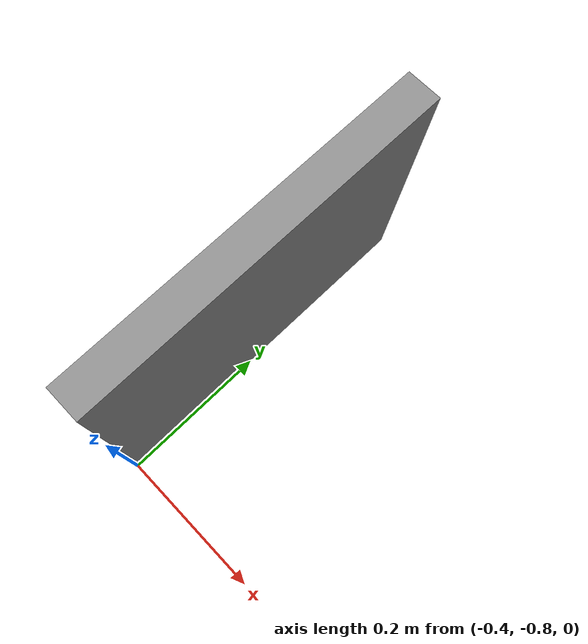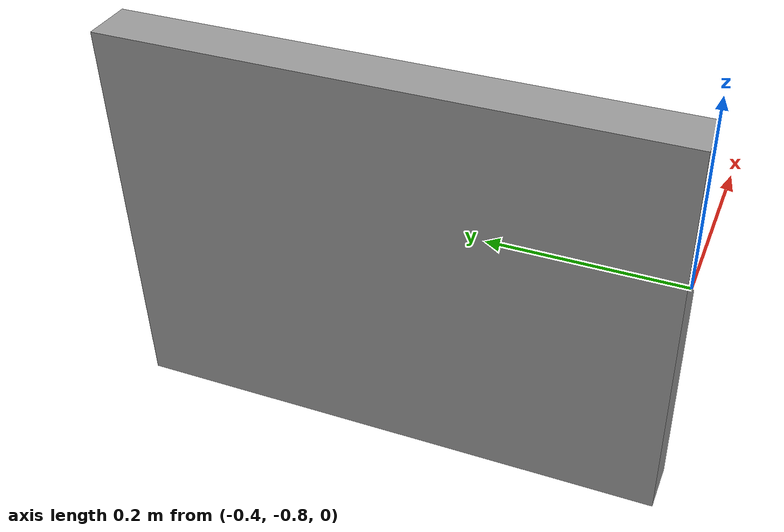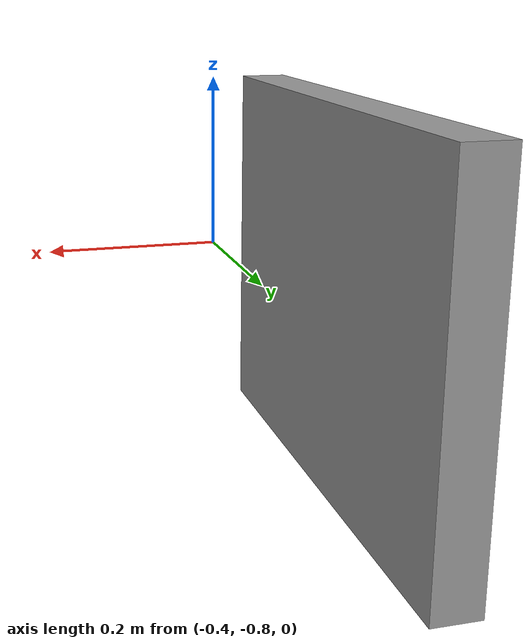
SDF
<?xml version='1.0'?>
<sdf version='1.6'>
  <model name='maze_model'>
      <link name='link_0'>
        <inertial>
          <mass>1</mass>
          <inertia>
            <ixx>0.166667</ixx>
            <ixy>0</ixy>
            <ixz>0</ixz>
            <iyy>0.166667</iyy>
            <iyz>0</iyz>
            <izz>0.166667</izz>
          </inertia>
          <pose frame=''>0 0 0 0 -0 0</pose>
        </inertial>
        <self_collide>0</self_collide>
        <enable_wind>0</enable_wind>
        <kinematic>0</kinematic>
        <pose frame=''>-0.463146 -0.530916 -0 0 -0 0</pose>
        <gravity>1</gravity>
        <visual name='visual'>
          <geometry>
            <box>
              <size>0.05 0.55 0.4</size>
            </box>
          </geometry>
          <material>
            <script>
              <name>Gazebo/Grey</name>
              <uri>file://media/materials/scripts/gazebo.material</uri>
            </script>
            <shader type='vertex'>
              <normal_map>__default__</normal_map>
            </shader>
            <ambient>0.3 0.3 0.3 1</ambient>
            <diffuse>0.7 0.7 0.7 1</diffuse>
            <specular>0.01 0.01 0.01 1</specular>
            <emissive>0 0 0 1</emissive>
          </material>
          <pose frame=''>0 0 0 0 -0 0</pose>
          <transparency>0</transparency>
          <cast_shadows>1</cast_shadows>
        </visual>
        <collision name='collision'>
          <laser_retro>0</laser_retro>
          <max_contacts>10</max_contacts>
          <pose frame=''>0 0 0 0 -0 0</pose>
          <geometry>
            <box>
              <size>0.05 0.55 0.4</size>
            </box>
          </geometry>
          <surface>
            <friction>
              <ode>
                <mu>1</mu>
                <mu2>1</mu2>
                <fdir1>0 0 0</fdir1>
                <slip1>0</slip1>
                <slip2>0</slip2>
              </ode>
              <torsional>
                <coefficient>1</coefficient>
                <patch_radius>0</patch_radius>
                <surface_radius>0</surface_radius>
                <use_patch_radius>1</use_patch_radius>
                <ode>
                  <slip>0</slip>
                </ode>
              </torsional>
            </friction>
            <bounce>
              <restitution_coefficient>0</restitution_coefficient>
              <threshold>1e+06</threshold>
            </bounce>
            <contact>
              <collide_without_contact>0</collide_without_contact>
              <collide_without_contact_bitmask>1</collide_without_contact_bitmask>
              <collide_bitmask>1</collide_bitmask>
              <ode>
                <soft_cfm>0</soft_cfm>
                <soft_erp>0.2</soft_erp>
                <kp>1e+13</kp>
                <kd>1</kd>
                <max_vel>0.01</max_vel>
                <min_depth>0</min_depth>
              </ode>
              <bullet>
                <split_impulse>1</split_impulse>
                <split_impulse_penetration_threshold>-0.01</split_impulse_penetration_threshold>
                <soft_cfm>0</soft_cfm>
                <soft_erp>0.2</soft_erp>
                <kp>1e+13</kp>
                <kd>1</kd>
              </bullet>
            </contact>
          </surface>
        </collision>
      </link>

      <link name='link_1'>
        <inertial>
          <mass>1</mass>
          <inertia>
            <ixx>0.166667</ixx>
            <ixy>0</ixy>
            <ixz>0</ixz>
            <iyy>0.166667</iyy>
            <iyz>0</iyz>
            <izz>0.166667</izz>
          </inertia>
          <pose frame=''>0 0 0 0 -0 0</pose>
        </inertial>
        <self_collide>0</self_collide>
        <enable_wind>0</enable_wind>
        <kinematic>0</kinematic>
        <pose frame=''>-0.463146 -0.530916 -0 0 -0 0</pose>
        <gravity>1</gravity>
        <visual name='visual'>
          <geometry>
            <box>
              <size>0.05 0.55 0.4</size>
            </box>
          </geometry>
          <material>
            <script>
              <name>Gazebo/Grey</name>
              <uri>file://media/materials/scripts/gazebo.material</uri>
            </script>
            <shader type='vertex'>
              <normal_map>__default__</normal_map>
            </shader>
            <ambient>0.3 0.3 0.3 1</ambient>
            <diffuse>0.7 0.7 0.7 1</diffuse>
            <specular>0.01 0.01 0.01 1</specular>
            <emissive>0 0 0 1</emissive>
          </material>
          <pose frame=''>0 0 0 0 -0 0</pose>
          <transparency>0</transparency>
          <cast_shadows>1</cast_shadows>
        </visual>
        <collision name='collision'>
          <laser_retro>0</laser_retro>
          <max_contacts>10</max_contacts>
          <pose frame=''>0 0 0 0 -0 0</pose>
          <geometry>
            <box>
              <size>0.05 0.55 0.4</size>
            </box>
          </geometry>
          <surface>
            <friction>
              <ode>
                <mu>1</mu>
                <mu2>1</mu2>
                <fdir1>0 0 0</fdir1>
                <slip1>0</slip1>
                <slip2>0</slip2>
              </ode>
              <torsional>
                <coefficient>1</coefficient>
                <patch_radius>0</patch_radius>
                <surface_radius>0</surface_radius>
                <use_patch_radius>1</use_patch_radius>
                <ode>
                  <slip>0</slip>
                </ode>
              </torsional>
            </friction>
            <bounce>
              <restitution_coefficient>0</restitution_coefficient>
              <threshold>1e+06</threshold>
            </bounce>
            <contact>
              <collide_without_contact>0</collide_without_contact>
              <collide_without_contact_bitmask>1</collide_without_contact_bitmask>
              <collide_bitmask>1</collide_bitmask>
              <ode>
                <soft_cfm>0</soft_cfm>
                <soft_erp>0.2</soft_erp>
                <kp>1e+13</kp>
                <kd>1</kd>
                <max_vel>0.01</max_vel>
                <min_depth>0</min_depth>
              </ode>
              <bullet>
                <split_impulse>1</split_impulse>
                <split_impulse_penetration_threshold>-0.01</split_impulse_penetration_threshold>
                <soft_cfm>0</soft_cfm>
                <soft_erp>0.2</soft_erp>
                <kp>1e+13</kp>
                <kd>1</kd>
              </bullet>
            </contact>
          </surface>
        </collision>
      </link>
      <link name='link_2'>
        <inertial>
          <mass>1</mass>
          <inertia>
            <ixx>0.166667</ixx>
            <ixy>0</ixy>
            <ixz>0</ixz>
            <iyy>0.166667</iyy>
            <iyz>0</iyz>
            <izz>0.166667</izz>
          </inertia>
          <pose frame=''>0 0 0 0 -0 0</pose>
        </inertial>
        <self_collide>0</self_collide>
        <enable_wind>0</enable_wind>
        <kinematic>0</kinematic>
        <pose frame=''>-0.463146 -0.530916 -0 0 -0 0</pose>
        <gravity>1</gravity>
        <visual name='visual'>
          <geometry>
            <box>
              <size>0.05 0.55 0.4</size>
            </box>
          </geometry>
          <material>
            <script>
              <name>Gazebo/Grey</name>
              <uri>file://media/materials/scripts/gazebo.material</uri>
            </script>
            <shader type='vertex'>
              <normal_map>__default__</normal_map>
            </shader>
            <ambient>0.3 0.3 0.3 1</ambient>
            <diffuse>0.7 0.7 0.7 1</diffuse>
            <specular>0.01 0.01 0.01 1</specular>
            <emissive>0 0 0 1</emissive>
          </material>
          <pose frame=''>0 0 0 0 -0 0</pose>
          <transparency>0</transparency>
          <cast_shadows>1</cast_shadows>
        </visual>
        <collision name='collision'>
          <laser_retro>0</laser_retro>
          <max_contacts>10</max_contacts>
          <pose frame=''>0 0 0 0 -0 0</pose>
          <geometry>
            <box>
              <size>0.05 0.55 0.4</size>
            </box>
          </geometry>
          <surface>
            <friction>
              <ode>
                <mu>1</mu>
                <mu2>1</mu2>
                <fdir1>0 0 0</fdir1>
                <slip1>0</slip1>
                <slip2>0</slip2>
              </ode>
              <torsional>
                <coefficient>1</coefficient>
                <patch_radius>0</patch_radius>
                <surface_radius>0</surface_radius>
                <use_patch_radius>1</use_patch_radius>
                <ode>
                  <slip>0</slip>
                </ode>
              </torsional>
            </friction>
            <bounce>
              <restitution_coefficient>0</restitution_coefficient>
              <threshold>1e+06</threshold>
            </bounce>
            <contact>
              <collide_without_contact>0</collide_without_contact>
              <collide_without_contact_bitmask>1</collide_without_contact_bitmask>
              <collide_bitmask>1</collide_bitmask>
              <ode>
                <soft_cfm>0</soft_cfm>
                <soft_erp>0.2</soft_erp>
                <kp>1e+13</kp>
                <kd>1</kd>
                <max_vel>0.01</max_vel>
                <min_depth>0</min_depth>
              </ode>
              <bullet>
                <split_impulse>1</split_impulse>
                <split_impulse_penetration_threshold>-0.01</split_impulse_penetration_threshold>
                <soft_cfm>0</soft_cfm>
                <soft_erp>0.2</soft_erp>
                <kp>1e+13</kp>
                <kd>1</kd>
              </bullet>
            </contact>
          </surface>
        </collision>
      </link>
      <link name='link_3'>
        <inertial>
          <mass>1</mass>
          <inertia>
            <ixx>0.166667</ixx>
            <ixy>0</ixy>
            <ixz>0</ixz>
            <iyy>0.166667</iyy>
            <iyz>0</iyz>
            <izz>0.166667</izz>
          </inertia>
          <pose frame=''>0 0 0 0 -0 0</pose>
        </inertial>
        <self_collide>0</self_collide>
        <enable_wind>0</enable_wind>
        <kinematic>0</kinematic>
        <pose frame=''>-0.463146 -0.530916 -0 0 -0 0</pose>
        <gravity>1</gravity>
        <visual name='visual'>
          <geometry>
            <box>
              <size>0.05 0.55 0.4</size>
            </box>
          </geometry>
          <material>
            <script>
              <name>Gazebo/Grey</name>
              <uri>file://media/materials/scripts/gazebo.material</uri>
            </script>
            <shader type='vertex'>
              <normal_map>__default__</normal_map>
            </shader>
            <ambient>0.3 0.3 0.3 1</ambient>
            <diffuse>0.7 0.7 0.7 1</diffuse>
            <specular>0.01 0.01 0.01 1</specular>
            <emissive>0 0 0 1</emissive>
          </material>
          <pose frame=''>0 0 0 0 -0 0</pose>
          <transparency>0</transparency>
          <cast_shadows>1</cast_shadows>
        </visual>
        <collision name='collision'>
          <laser_retro>0</laser_retro>
          <max_contacts>10</max_contacts>
          <pose frame=''>0 0 0 0 -0 0</pose>
          <geometry>
            <box>
              <size>0.05 0.55 0.4</size>
            </box>
          </geometry>
          <surface>
            <friction>
              <ode>
                <mu>1</mu>
                <mu2>1</mu2>
                <fdir1>0 0 0</fdir1>
                <slip1>0</slip1>
                <slip2>0</slip2>
              </ode>
              <torsional>
                <coefficient>1</coefficient>
                <patch_radius>0</patch_radius>
                <surface_radius>0</surface_radius>
                <use_patch_radius>1</use_patch_radius>
                <ode>
                  <slip>0</slip>
                </ode>
              </torsional>
            </friction>
            <bounce>
              <restitution_coefficient>0</restitution_coefficient>
              <threshold>1e+06</threshold>
            </bounce>
            <contact>
              <collide_without_contact>0</collide_without_contact>
              <collide_without_contact_bitmask>1</collide_without_contact_bitmask>
              <collide_bitmask>1</collide_bitmask>
              <ode>
                <soft_cfm>0</soft_cfm>
                <soft_erp>0.2</soft_erp>
                <kp>1e+13</kp>
                <kd>1</kd>
                <max_vel>0.01</max_vel>
                <min_depth>0</min_depth>
              </ode>
              <bullet>
                <split_impulse>1</split_impulse>
                <split_impulse_penetration_threshold>-0.01</split_impulse_penetration_threshold>
                <soft_cfm>0</soft_cfm>
                <soft_erp>0.2</soft_erp>
                <kp>1e+13</kp>
                <kd>1</kd>
              </bullet>
            </contact>
          </surface>
        </collision>
      </link>
      <link name='link_4'>
        <inertial>
          <mass>1</mass>
          <inertia>
            <ixx>0.166667</ixx>
            <ixy>0</ixy>
            <ixz>0</ixz>
            <iyy>0.166667</iyy>
            <iyz>0</iyz>
            <izz>0.166667</izz>
          </inertia>
          <pose frame=''>0 0 0 0 -0 0</pose>
        </inertial>
        <self_collide>0</self_collide>
        <enable_wind>0</enable_wind>
        <kinematic>0</kinematic>
        <pose frame=''>-0.463146 -0.530916 -0 0 -0 0</pose>
        <gravity>1</gravity>
        <visual name='visual'>
          <geometry>
            <box>
              <size>0.05 0.55 0.4</size>
            </box>
          </geometry>
          <material>
            <script>
              <name>Gazebo/Grey</name>
              <uri>file://media/materials/scripts/gazebo.material</uri>
            </script>
            <shader type='vertex'>
              <normal_map>__default__</normal_map>
            </shader>
            <ambient>0.3 0.3 0.3 1</ambient>
            <diffuse>0.7 0.7 0.7 1</diffuse>
            <specular>0.01 0.01 0.01 1</specular>
            <emissive>0 0 0 1</emissive>
          </material>
          <pose frame=''>0 0 0 0 -0 0</pose>
          <transparency>0</transparency>
          <cast_shadows>1</cast_shadows>
        </visual>
        <collision name='collision'>
          <laser_retro>0</laser_retro>
          <max_contacts>10</max_contacts>
          <pose frame=''>0 0 0 0 -0 0</pose>
          <geometry>
            <box>
              <size>0.05 0.55 0.4</size>
            </box>
          </geometry>
          <surface>
            <friction>
              <ode>
                <mu>1</mu>
                <mu2>1</mu2>
                <fdir1>0 0 0</fdir1>
                <slip1>0</slip1>
                <slip2>0</slip2>
              </ode>
              <torsional>
                <coefficient>1</coefficient>
                <patch_radius>0</patch_radius>
                <surface_radius>0</surface_radius>
                <use_patch_radius>1</use_patch_radius>
                <ode>
                  <slip>0</slip>
                </ode>
              </torsional>
            </friction>
            <bounce>
              <restitution_coefficient>0</restitution_coefficient>
              <threshold>1e+06</threshold>
            </bounce>
            <contact>
              <collide_without_contact>0</collide_without_contact>
              <collide_without_contact_bitmask>1</collide_without_contact_bitmask>
              <collide_bitmask>1</collide_bitmask>
              <ode>
                <soft_cfm>0</soft_cfm>
                <soft_erp>0.2</soft_erp>
                <kp>1e+13</kp>
                <kd>1</kd>
                <max_vel>0.01</max_vel>
                <min_depth>0</min_depth>
              </ode>
              <bullet>
                <split_impulse>1</split_impulse>
                <split_impulse_penetration_threshold>-0.01</split_impulse_penetration_threshold>
                <soft_cfm>0</soft_cfm>
                <soft_erp>0.2</soft_erp>
                <kp>1e+13</kp>
                <kd>1</kd>
              </bullet>
            </contact>
          </surface>
        </collision>
      </link>
      <link name='link5'>
        <inertial>
          <mass>1</mass>
          <inertia>
            <ixx>0.166667</ixx>
            <ixy>0</ixy>
            <ixz>0</ixz>
            <iyy>0.166667</iyy>
            <iyz>0</iyz>
            <izz>0.166667</izz>
          </inertia>
          <pose frame=''>0 0 0 0 -0 0</pose>
        </inertial>
        <self_collide>0</self_collide>
        <enable_wind>0</enable_wind>
        <kinematic>0</kinematic>
        <pose frame=''>-0.463146 -0.530916 -0 0 -0 0</pose>
        <gravity>1</gravity>
        <visual name='visual'>
          <geometry>
            <box>
              <size>0.05 0.55 0.4</size>
            </box>
          </geometry>
          <material>
            <script>
              <name>Gazebo/Grey</name>
              <uri>file://media/materials/scripts/gazebo.material</uri>
            </script>
            <shader type='vertex'>
              <normal_map>__default__</normal_map>
            </shader>
            <ambient>0.3 0.3 0.3 1</ambient>
            <diffuse>0.7 0.7 0.7 1</diffuse>
            <specular>0.01 0.01 0.01 1</specular>
            <emissive>0 0 0 1</emissive>
          </material>
          <pose frame=''>0 0 0 0 -0 0</pose>
          <transparency>0</transparency>
          <cast_shadows>1</cast_shadows>
        </visual>
        <collision name='collision'>
          <laser_retro>0</laser_retro>
          <max_contacts>10</max_contacts>
          <pose frame=''>0 0 0 0 -0 0</pose>
          <geometry>
            <box>
              <size>0.05 0.55 0.4</size>
            </box>
          </geometry>
          <surface>
            <friction>
              <ode>
                <mu>1</mu>
                <mu2>1</mu2>
                <fdir1>0 0 0</fdir1>
                <slip1>0</slip1>
                <slip2>0</slip2>
              </ode>
              <torsional>
                <coefficient>1</coefficient>
                <patch_radius>0</patch_radius>
                <surface_radius>0</surface_radius>
                <use_patch_radius>1</use_patch_radius>
                <ode>
                  <slip>0</slip>
                </ode>
              </torsional>
            </friction>
            <bounce>
              <restitution_coefficient>0</restitution_coefficient>
              <threshold>1e+06</threshold>
            </bounce>
            <contact>
              <collide_without_contact>0</collide_without_contact>
              <collide_without_contact_bitmask>1</collide_without_contact_bitmask>
              <collide_bitmask>1</collide_bitmask>
              <ode>
                <soft_cfm>0</soft_cfm>
                <soft_erp>0.2</soft_erp>
                <kp>1e+13</kp>
                <kd>1</kd>
                <max_vel>0.01</max_vel>
                <min_depth>0</min_depth>
              </ode>
              <bullet>
                <split_impulse>1</split_impulse>
                <split_impulse_penetration_threshold>-0.01</split_impulse_penetration_threshold>
                <soft_cfm>0</soft_cfm>
                <soft_erp>0.2</soft_erp>
                <kp>1e+13</kp>
                <kd>1</kd>
              </bullet>
            </contact>
          </surface>
        </collision>
      </link>
      <link name='link_6'>
        <inertial>
          <mass>1</mass>
          <inertia>
            <ixx>0.166667</ixx>
            <ixy>0</ixy>
            <ixz>0</ixz>
            <iyy>0.166667</iyy>
            <iyz>0</iyz>
            <izz>0.166667</izz>
          </inertia>
          <pose frame=''>0 0 0 0 -0 0</pose>
        </inertial>
        <self_collide>0</self_collide>
        <enable_wind>0</enable_wind>
        <kinematic>0</kinematic>
        <pose frame=''>-0.463146 -0.530916 -0 0 -0 0</pose>
        <gravity>1</gravity>
        <visual name='visual'>
          <geometry>
            <box>
              <size>0.05 0.55 0.4</size>
            </box>
          </geometry>
          <material>
            <script>
              <name>Gazebo/Grey</name>
              <uri>file://media/materials/scripts/gazebo.material</uri>
            </script>
            <shader type='vertex'>
              <normal_map>__default__</normal_map>
            </shader>
            <ambient>0.3 0.3 0.3 1</ambient>
            <diffuse>0.7 0.7 0.7 1</diffuse>
            <specular>0.01 0.01 0.01 1</specular>
            <emissive>0 0 0 1</emissive>
          </material>
          <pose frame=''>0 0 0 0 -0 0</pose>
          <transparency>0</transparency>
          <cast_shadows>1</cast_shadows>
        </visual>
        <collision name='collision'>
          <laser_retro>0</laser_retro>
          <max_contacts>10</max_contacts>
          <pose frame=''>0 0 0 0 -0 0</pose>
          <geometry>
            <box>
              <size>0.05 0.55 0.4</size>
            </box>
          </geometry>
          <surface>
            <friction>
              <ode>
                <mu>1</mu>
                <mu2>1</mu2>
                <fdir1>0 0 0</fdir1>
                <slip1>0</slip1>
                <slip2>0</slip2>
              </ode>
              <torsional>
                <coefficient>1</coefficient>
                <patch_radius>0</patch_radius>
                <surface_radius>0</surface_radius>
                <use_patch_radius>1</use_patch_radius>
                <ode>
                  <slip>0</slip>
                </ode>
              </torsional>
            </friction>
            <bounce>
              <restitution_coefficient>0</restitution_coefficient>
              <threshold>1e+06</threshold>
            </bounce>
            <contact>
              <collide_without_contact>0</collide_without_contact>
              <collide_without_contact_bitmask>1</collide_without_contact_bitmask>
              <collide_bitmask>1</collide_bitmask>
              <ode>
                <soft_cfm>0</soft_cfm>
                <soft_erp>0.2</soft_erp>
                <kp>1e+13</kp>
                <kd>1</kd>
                <max_vel>0.01</max_vel>
                <min_depth>0</min_depth>
              </ode>
              <bullet>
                <split_impulse>1</split_impulse>
                <split_impulse_penetration_threshold>-0.01</split_impulse_penetration_threshold>
                <soft_cfm>0</soft_cfm>
                <soft_erp>0.2</soft_erp>
                <kp>1e+13</kp>
                <kd>1</kd>
              </bullet>
            </contact>
          </surface>
        </collision>
      </link>
      <link name='link_7'>
        <inertial>
          <mass>1</mass>
          <inertia>
            <ixx>0.166667</ixx>
            <ixy>0</ixy>
            <ixz>0</ixz>
            <iyy>0.166667</iyy>
            <iyz>0</iyz>
            <izz>0.166667</izz>
          </inertia>
          <pose frame=''>0 0 0 0 -0 0</pose>
        </inertial>
        <self_collide>0</self_collide>
        <enable_wind>0</enable_wind>
        <kinematic>0</kinematic>
        <pose frame=''>-0.463146 -0.530916 -0 0 -0 0</pose>
        <gravity>1</gravity>
        <visual name='visual'>
          <geometry>
            <box>
              <size>0.05 0.55 0.4</size>
            </box>
          </geometry>
          <material>
            <script>
              <name>Gazebo/Grey</name>
              <uri>file://media/materials/scripts/gazebo.material</uri>
            </script>
            <shader type='vertex'>
              <normal_map>__default__</normal_map>
            </shader>
            <ambient>0.3 0.3 0.3 1</ambient>
            <diffuse>0.7 0.7 0.7 1</diffuse>
            <specular>0.01 0.01 0.01 1</specular>
            <emissive>0 0 0 1</emissive>
          </material>
          <pose frame=''>0 0 0 0 -0 0</pose>
          <transparency>0</transparency>
          <cast_shadows>1</cast_shadows>
        </visual>
        <collision name='collision'>
          <laser_retro>0</laser_retro>
          <max_contacts>10</max_contacts>
          <pose frame=''>0 0 0 0 -0 0</pose>
          <geometry>
            <box>
              <size>0.05 0.55 0.4</size>
            </box>
          </geometry>
          <surface>
            <friction>
              <ode>
                <mu>1</mu>
                <mu2>1</mu2>
                <fdir1>0 0 0</fdir1>
                <slip1>0</slip1>
                <slip2>0</slip2>
              </ode>
              <torsional>
                <coefficient>1</coefficient>
                <patch_radius>0</patch_radius>
                <surface_radius>0</surface_radius>
                <use_patch_radius>1</use_patch_radius>
                <ode>
                  <slip>0</slip>
                </ode>
              </torsional>
            </friction>
            <bounce>
              <restitution_coefficient>0</restitution_coefficient>
              <threshold>1e+06</threshold>
            </bounce>
            <contact>
              <collide_without_contact>0</collide_without_contact>
              <collide_without_contact_bitmask>1</collide_without_contact_bitmask>
              <collide_bitmask>1</collide_bitmask>
              <ode>
                <soft_cfm>0</soft_cfm>
                <soft_erp>0.2</soft_erp>
                <kp>1e+13</kp>
                <kd>1</kd>
                <max_vel>0.01</max_vel>
                <min_depth>0</min_depth>
              </ode>
              <bullet>
                <split_impulse>1</split_impulse>
                <split_impulse_penetration_threshold>-0.01</split_impulse_penetration_threshold>
                <soft_cfm>0</soft_cfm>
                <soft_erp>0.2</soft_erp>
                <kp>1e+13</kp>
                <kd>1</kd>
              </bullet>
            </contact>
          </surface>
        </collision>
      </link>
      <link name='link_8'>
        <inertial>
          <mass>1</mass>
          <inertia>
            <ixx>0.166667</ixx>
            <ixy>0</ixy>
            <ixz>0</ixz>
            <iyy>0.166667</iyy>
            <iyz>0</iyz>
            <izz>0.166667</izz>
          </inertia>
          <pose frame=''>0 0 0 0 -0 0</pose>
        </inertial>
        <self_collide>0</self_collide>
        <enable_wind>0</enable_wind>
        <kinematic>0</kinematic>
        <pose frame=''>-0.463146 -0.530916 -0 0 -0 0</pose>
        <gravity>1</gravity>
        <visual name='visual'>
          <geometry>
            <box>
              <size>0.05 0.55 0.4</size>
            </box>
          </geometry>
          <material>
            <script>
              <name>Gazebo/Grey</name>
              <uri>file://media/materials/scripts/gazebo.material</uri>
            </script>
            <shader type='vertex'>
              <normal_map>__default__</normal_map>
            </shader>
            <ambient>0.3 0.3 0.3 1</ambient>
            <diffuse>0.7 0.7 0.7 1</diffuse>
            <specular>0.01 0.01 0.01 1</specular>
            <emissive>0 0 0 1</emissive>
          </material>
          <pose frame=''>0 0 0 0 -0 0</pose>
          <transparency>0</transparency>
          <cast_shadows>1</cast_shadows>
        </visual>
        <collision name='collision'>
          <laser_retro>0</laser_retro>
          <max_contacts>10</max_contacts>
          <pose frame=''>0 0 0 0 -0 0</pose>
          <geometry>
            <box>
              <size>0.05 0.55 0.4</size>
            </box>
          </geometry>
          <surface>
            <friction>
              <ode>
                <mu>1</mu>
                <mu2>1</mu2>
                <fdir1>0 0 0</fdir1>
                <slip1>0</slip1>
                <slip2>0</slip2>
              </ode>
              <torsional>
                <coefficient>1</coefficient>
                <patch_radius>0</patch_radius>
                <surface_radius>0</surface_radius>
                <use_patch_radius>1</use_patch_radius>
                <ode>
                  <slip>0</slip>
                </ode>
              </torsional>
            </friction>
            <bounce>
              <restitution_coefficient>0</restitution_coefficient>
              <threshold>1e+06</threshold>
            </bounce>
            <contact>
              <collide_without_contact>0</collide_without_contact>
              <collide_without_contact_bitmask>1</collide_without_contact_bitmask>
              <collide_bitmask>1</collide_bitmask>
              <ode>
                <soft_cfm>0</soft_cfm>
                <soft_erp>0.2</soft_erp>
                <kp>1e+13</kp>
                <kd>1</kd>
                <max_vel>0.01</max_vel>
                <min_depth>0</min_depth>
              </ode>
              <bullet>
                <split_impulse>1</split_impulse>
                <split_impulse_penetration_threshold>-0.01</split_impulse_penetration_threshold>
                <soft_cfm>0</soft_cfm>
                <soft_erp>0.2</soft_erp>
                <kp>1e+13</kp>
                <kd>1</kd>
              </bullet>
            </contact>
          </surface>
        </collision>
      </link>

      <link name='link_9'>
        <inertial>
          <mass>1</mass>
          <inertia>
            <ixx>0.166667</ixx>
            <ixy>0</ixy>
            <ixz>0</ixz>
            <iyy>0.166667</iyy>
            <iyz>0</iyz>
            <izz>0.166667</izz>
          </inertia>
          <pose frame=''>0 0 0 0 -0 0</pose>
        </inertial>
        <self_collide>0</self_collide>
        <enable_wind>0</enable_wind>
        <kinematic>0</kinematic>
        <pose frame=''>-0.463146 -0.530916 -0 0 -0 0</pose>
        <gravity>1</gravity>
        <visual name='visual'>
          <geometry>
            <box>
              <size>0.05 0.55 0.4</size>
            </box>
          </geometry>
          <material>
            <script>
              <name>Gazebo/Grey</name>
              <uri>file://media/materials/scripts/gazebo.material</uri>
            </script>
            <shader type='vertex'>
              <normal_map>__default__</normal_map>
            </shader>
            <ambient>0.3 0.3 0.3 1</ambient>
            <diffuse>0.7 0.7 0.7 1</diffuse>
            <specular>0.01 0.01 0.01 1</specular>
            <emissive>0 0 0 1</emissive>
          </material>
          <pose frame=''>0 0 0 0 -0 0</pose>
          <transparency>0</transparency>
          <cast_shadows>1</cast_shadows>
        </visual>
        <collision name='collision'>
          <laser_retro>0</laser_retro>
          <max_contacts>10</max_contacts>
          <pose frame=''>0 0 0 0 -0 0</pose>
          <geometry>
            <box>
              <size>0.05 0.55 0.4</size>
            </box>
          </geometry>
          <surface>
            <friction>
              <ode>
                <mu>1</mu>
                <mu2>1</mu2>
                <fdir1>0 0 0</fdir1>
                <slip1>0</slip1>
                <slip2>0</slip2>
              </ode>
              <torsional>
                <coefficient>1</coefficient>
                <patch_radius>0</patch_radius>
                <surface_radius>0</surface_radius>
                <use_patch_radius>1</use_patch_radius>
                <ode>
                  <slip>0</slip>
                </ode>
              </torsional>
            </friction>
            <bounce>
              <restitution_coefficient>0</restitution_coefficient>
              <threshold>1e+06</threshold>
            </bounce>
            <contact>
              <collide_without_contact>0</collide_without_contact>
              <collide_without_contact_bitmask>1</collide_without_contact_bitmask>
              <collide_bitmask>1</collide_bitmask>
              <ode>
                <soft_cfm>0</soft_cfm>
                <soft_erp>0.2</soft_erp>
                <kp>1e+13</kp>
                <kd>1</kd>
                <max_vel>0.01</max_vel>
                <min_depth>0</min_depth>
              </ode>
              <bullet>
                <split_impulse>1</split_impulse>
                <split_impulse_penetration_threshold>-0.01</split_impulse_penetration_threshold>
                <soft_cfm>0</soft_cfm>
                <soft_erp>0.2</soft_erp>
                <kp>1e+13</kp>
                <kd>1</kd>
              </bullet>
            </contact>
          </surface>
        </collision>
      </link>

      <link name='link_10'>
        <inertial>
          <mass>1</mass>
          <inertia>
            <ixx>0.166667</ixx>
            <ixy>0</ixy>
            <ixz>0</ixz>
            <iyy>0.166667</iyy>
            <iyz>0</iyz>
            <izz>0.166667</izz>
          </inertia>
          <pose frame=''>0 0 0 0 -0 0</pose>
        </inertial>
        <self_collide>0</self_collide>
        <enable_wind>0</enable_wind>
        <kinematic>0</kinematic>
        <pose frame=''>-0.463146 -0.530916 -0 0 -0 0</pose>
        <gravity>1</gravity>
        <visual name='visual'>
          <geometry>
            <box>
              <size>0.05 0.55 0.4</size>
            </box>
          </geometry>
          <material>
            <script>
              <name>Gazebo/Grey</name>
              <uri>file://media/materials/scripts/gazebo.material</uri>
            </script>
            <shader type='vertex'>
              <normal_map>__default__</normal_map>
            </shader>
            <ambient>0.3 0.3 0.3 1</ambient>
            <diffuse>0.7 0.7 0.7 1</diffuse>
            <specular>0.01 0.01 0.01 1</specular>
            <emissive>0 0 0 1</emissive>
          </material>
          <pose frame=''>0 0 0 0 -0 0</pose>
          <transparency>0</transparency>
          <cast_shadows>1</cast_shadows>
        </visual>
        <collision name='collision'>
          <laser_retro>0</laser_retro>
          <max_contacts>10</max_contacts>
          <pose frame=''>0 0 0 0 -0 0</pose>
          <geometry>
            <box>
              <size>0.05 0.55 0.4</size>
            </box>
          </geometry>
          <surface>
            <friction>
              <ode>
                <mu>1</mu>
                <mu2>1</mu2>
                <fdir1>0 0 0</fdir1>
                <slip1>0</slip1>
                <slip2>0</slip2>
              </ode>
              <torsional>
                <coefficient>1</coefficient>
                <patch_radius>0</patch_radius>
                <surface_radius>0</surface_radius>
                <use_patch_radius>1</use_patch_radius>
                <ode>
                  <slip>0</slip>
                </ode>
              </torsional>
            </friction>
            <bounce>
              <restitution_coefficient>0</restitution_coefficient>
              <threshold>1e+06</threshold>
            </bounce>
            <contact>
              <collide_without_contact>0</collide_without_contact>
              <collide_without_contact_bitmask>1</collide_without_contact_bitmask>
              <collide_bitmask>1</collide_bitmask>
              <ode>
                <soft_cfm>0</soft_cfm>
                <soft_erp>0.2</soft_erp>
                <kp>1e+13</kp>
                <kd>1</kd>
                <max_vel>0.01</max_vel>
                <min_depth>0</min_depth>
              </ode>
              <bullet>
                <split_impulse>1</split_impulse>
                <split_impulse_penetration_threshold>-0.01</split_impulse_penetration_threshold>
                <soft_cfm>0</soft_cfm>
                <soft_erp>0.2</soft_erp>
                <kp>1e+13</kp>
                <kd>1</kd>
              </bullet>
            </contact>
          </surface>
        </collision>
      </link>

      <link name='link_11'>
        <inertial>
          <mass>1</mass>
          <inertia>
            <ixx>0.166667</ixx>
            <ixy>0</ixy>
            <ixz>0</ixz>
            <iyy>0.166667</iyy>
            <iyz>0</iyz>
            <izz>0.166667</izz>
          </inertia>
          <pose frame=''>0 0 0 0 -0 0</pose>
        </inertial>
        <self_collide>0</self_collide>
        <enable_wind>0</enable_wind>
        <kinematic>0</kinematic>
        <pose frame=''>-0.463146 -0.530916 -0 0 -0 0</pose>
        <gravity>1</gravity>
        <visual name='visual'>
          <geometry>
            <box>
              <size>0.05 0.55 0.4</size>
            </box>
          </geometry>
          <material>
            <script>
              <name>Gazebo/Grey</name>
              <uri>file://media/materials/scripts/gazebo.material</uri>
            </script>
            <shader type='vertex'>
              <normal_map>__default__</normal_map>
            </shader>
            <ambient>0.3 0.3 0.3 1</ambient>
            <diffuse>0.7 0.7 0.7 1</diffuse>
            <specular>0.01 0.01 0.01 1</specular>
            <emissive>0 0 0 1</emissive>
          </material>
          <pose frame=''>0 0 0 0 -0 0</pose>
          <transparency>0</transparency>
          <cast_shadows>1</cast_shadows>
        </visual>
        <collision name='collision'>
          <laser_retro>0</laser_retro>
          <max_contacts>10</max_contacts>
          <pose frame=''>0 0 0 0 -0 0</pose>
          <geometry>
            <box>
              <size>0.05 0.55 0.4</size>
            </box>
          </geometry>
          <surface>
            <friction>
              <ode>
                <mu>1</mu>
                <mu2>1</mu2>
                <fdir1>0 0 0</fdir1>
                <slip1>0</slip1>
                <slip2>0</slip2>
              </ode>
              <torsional>
                <coefficient>1</coefficient>
                <patch_radius>0</patch_radius>
                <surface_radius>0</surface_radius>
                <use_patch_radius>1</use_patch_radius>
                <ode>
                  <slip>0</slip>
                </ode>
              </torsional>
            </friction>
            <bounce>
              <restitution_coefficient>0</restitution_coefficient>
              <threshold>1e+06</threshold>
            </bounce>
            <contact>
              <collide_without_contact>0</collide_without_contact>
              <collide_without_contact_bitmask>1</collide_without_contact_bitmask>
              <collide_bitmask>1</collide_bitmask>
              <ode>
                <soft_cfm>0</soft_cfm>
                <soft_erp>0.2</soft_erp>
                <kp>1e+13</kp>
                <kd>1</kd>
                <max_vel>0.01</max_vel>
                <min_depth>0</min_depth>
              </ode>
              <bullet>
                <split_impulse>1</split_impulse>
                <split_impulse_penetration_threshold>-0.01</split_impulse_penetration_threshold>
                <soft_cfm>0</soft_cfm>
                <soft_erp>0.2</soft_erp>
                <kp>1e+13</kp>
                <kd>1</kd>
              </bullet>
            </contact>
          </surface>
        </collision>
      </link>

      <link name='link_13'>
        <inertial>
          <mass>1</mass>
          <inertia>
            <ixx>0.166667</ixx>
            <ixy>0</ixy>
            <ixz>0</ixz>
            <iyy>0.166667</iyy>
            <iyz>0</iyz>
            <izz>0.166667</izz>
          </inertia>
          <pose frame=''>0 0 0 0 -0 0</pose>
        </inertial>
        <self_collide>0</self_collide>
        <enable_wind>0</enable_wind>
        <kinematic>0</kinematic>
        <pose frame=''>-0.463146 -0.530916 -0 0 -0 0</pose>
        <gravity>1</gravity>
        <visual name='visual'>
          <geometry>
            <box>
              <size>0.05 0.55 0.4</size>
            </box>
          </geometry>
          <material>
            <script>
              <name>Gazebo/Grey</name>
              <uri>file://media/materials/scripts/gazebo.material</uri>
            </script>
            <shader type='vertex'>
              <normal_map>__default__</normal_map>
            </shader>
            <ambient>0.3 0.3 0.3 1</ambient>
            <diffuse>0.7 0.7 0.7 1</diffuse>
            <specular>0.01 0.01 0.01 1</specular>
            <emissive>0 0 0 1</emissive>
          </material>
          <pose frame=''>0 0 0 0 -0 0</pose>
          <transparency>0</transparency>
          <cast_shadows>1</cast_shadows>
        </visual>
        <collision name='collision'>
          <laser_retro>0</laser_retro>
          <max_contacts>10</max_contacts>
          <pose frame=''>0 0 0 0 -0 0</pose>
          <geometry>
            <box>
              <size>0.05 0.55 0.4</size>
            </box>
          </geometry>
          <surface>
            <friction>
              <ode>
                <mu>1</mu>
                <mu2>1</mu2>
                <fdir1>0 0 0</fdir1>
                <slip1>0</slip1>
                <slip2>0</slip2>
              </ode>
              <torsional>
                <coefficient>1</coefficient>
                <patch_radius>0</patch_radius>
                <surface_radius>0</surface_radius>
                <use_patch_radius>1</use_patch_radius>
                <ode>
                  <slip>0</slip>
                </ode>
              </torsional>
            </friction>
            <bounce>
              <restitution_coefficient>0</restitution_coefficient>
              <threshold>1e+06</threshold>
            </bounce>
            <contact>
              <collide_without_contact>0</collide_without_contact>
              <collide_without_contact_bitmask>1</collide_without_contact_bitmask>
              <collide_bitmask>1</collide_bitmask>
              <ode>
                <soft_cfm>0</soft_cfm>
                <soft_erp>0.2</soft_erp>
                <kp>1e+13</kp>
                <kd>1</kd>
                <max_vel>0.01</max_vel>
                <min_depth>0</min_depth>
              </ode>
              <bullet>
                <split_impulse>1</split_impulse>
                <split_impulse_penetration_threshold>-0.01</split_impulse_penetration_threshold>
                <soft_cfm>0</soft_cfm>
                <soft_erp>0.2</soft_erp>
                <kp>1e+13</kp>
                <kd>1</kd>
              </bullet>
            </contact>
          </surface>
        </collision>
      </link>

      <link name='link_14'>
        <inertial>
          <mass>1</mass>
          <inertia>
            <ixx>0.166667</ixx>
            <ixy>0</ixy>
            <ixz>0</ixz>
            <iyy>0.166667</iyy>
            <iyz>0</iyz>
            <izz>0.166667</izz>
          </inertia>
          <pose frame=''>0 0 0 0 -0 0</pose>
        </inertial>
        <self_collide>0</self_collide>
        <enable_wind>0</enable_wind>
        <kinematic>0</kinematic>
        <pose frame=''>-0.463146 -0.530916 -0 0 -0 0</pose>
        <gravity>1</gravity>
        <visual name='visual'>
          <geometry>
            <box>
              <size>0.05 0.55 0.4</size>
            </box>
          </geometry>
          <material>
            <script>
              <name>Gazebo/Grey</name>
              <uri>file://media/materials/scripts/gazebo.material</uri>
            </script>
            <shader type='vertex'>
              <normal_map>__default__</normal_map>
            </shader>
            <ambient>0.3 0.3 0.3 1</ambient>
            <diffuse>0.7 0.7 0.7 1</diffuse>
            <specular>0.01 0.01 0.01 1</specular>
            <emissive>0 0 0 1</emissive>
          </material>
          <pose frame=''>0 0 0 0 -0 0</pose>
          <transparency>0</transparency>
          <cast_shadows>1</cast_shadows>
        </visual>
        <collision name='collision'>
          <laser_retro>0</laser_retro>
          <max_contacts>10</max_contacts>
          <pose frame=''>0 0 0 0 -0 0</pose>
          <geometry>
            <box>
              <size>0.05 0.55 0.4</size>
            </box>
          </geometry>
          <surface>
            <friction>
              <ode>
                <mu>1</mu>
                <mu2>1</mu2>
                <fdir1>0 0 0</fdir1>
                <slip1>0</slip1>
                <slip2>0</slip2>
              </ode>
              <torsional>
                <coefficient>1</coefficient>
                <patch_radius>0</patch_radius>
                <surface_radius>0</surface_radius>
                <use_patch_radius>1</use_patch_radius>
                <ode>
                  <slip>0</slip>
                </ode>
              </torsional>
            </friction>
            <bounce>
              <restitution_coefficient>0</restitution_coefficient>
              <threshold>1e+06</threshold>
            </bounce>
            <contact>
              <collide_without_contact>0</collide_without_contact>
              <collide_without_contact_bitmask>1</collide_without_contact_bitmask>
              <collide_bitmask>1</collide_bitmask>
              <ode>
                <soft_cfm>0</soft_cfm>
                <soft_erp>0.2</soft_erp>
                <kp>1e+13</kp>
                <kd>1</kd>
                <max_vel>0.01</max_vel>
                <min_depth>0</min_depth>
              </ode>
              <bullet>
                <split_impulse>1</split_impulse>
                <split_impulse_penetration_threshold>-0.01</split_impulse_penetration_threshold>
                <soft_cfm>0</soft_cfm>
                <soft_erp>0.2</soft_erp>
                <kp>1e+13</kp>
                <kd>1</kd>
              </bullet>
            </contact>
          </surface>
        </collision>
      </link>

      <link name='link_15'>
        <inertial>
          <mass>1</mass>
          <inertia>
            <ixx>0.166667</ixx>
            <ixy>0</ixy>
            <ixz>0</ixz>
            <iyy>0.166667</iyy>
            <iyz>0</iyz>
            <izz>0.166667</izz>
          </inertia>
          <pose frame=''>0 0 0 0 -0 0</pose>
        </inertial>
        <self_collide>0</self_collide>
        <enable_wind>0</enable_wind>
        <kinematic>0</kinematic>
        <pose frame=''>-0.463146 -0.530916 -0 0 -0 0</pose>
        <gravity>1</gravity>
        <visual name='visual'>
          <geometry>
            <box>
              <size>0.05 0.55 0.4</size>
            </box>
          </geometry>
          <material>
            <script>
              <name>Gazebo/Grey</name>
              <uri>file://media/materials/scripts/gazebo.material</uri>
            </script>
            <shader type='vertex'>
              <normal_map>__default__</normal_map>
            </shader>
            <ambient>0.3 0.3 0.3 1</ambient>
            <diffuse>0.7 0.7 0.7 1</diffuse>
            <specular>0.01 0.01 0.01 1</specular>
            <emissive>0 0 0 1</emissive>
          </material>
          <pose frame=''>0 0 0 0 -0 0</pose>
          <transparency>0</transparency>
          <cast_shadows>1</cast_shadows>
        </visual>
        <collision name='collision'>
          <laser_retro>0</laser_retro>
          <max_contacts>10</max_contacts>
          <pose frame=''>0 0 0 0 -0 0</pose>
          <geometry>
            <box>
              <size>0.05 0.55 0.4</size>
            </box>
          </geometry>
          <surface>
            <friction>
              <ode>
                <mu>1</mu>
                <mu2>1</mu2>
                <fdir1>0 0 0</fdir1>
                <slip1>0</slip1>
                <slip2>0</slip2>
              </ode>
              <torsional>
                <coefficient>1</coefficient>
                <patch_radius>0</patch_radius>
                <surface_radius>0</surface_radius>
                <use_patch_radius>1</use_patch_radius>
                <ode>
                  <slip>0</slip>
                </ode>
              </torsional>
            </friction>
            <bounce>
              <restitution_coefficient>0</restitution_coefficient>
              <threshold>1e+06</threshold>
            </bounce>
            <contact>
              <collide_without_contact>0</collide_without_contact>
              <collide_without_contact_bitmask>1</collide_without_contact_bitmask>
              <collide_bitmask>1</collide_bitmask>
              <ode>
                <soft_cfm>0</soft_cfm>
                <soft_erp>0.2</soft_erp>
                <kp>1e+13</kp>
                <kd>1</kd>
                <max_vel>0.01</max_vel>
                <min_depth>0</min_depth>
              </ode>
              <bullet>
                <split_impulse>1</split_impulse>
                <split_impulse_penetration_threshold>-0.01</split_impulse_penetration_threshold>
                <soft_cfm>0</soft_cfm>
                <soft_erp>0.2</soft_erp>
                <kp>1e+13</kp>
                <kd>1</kd>
              </bullet>
            </contact>
          </surface>
        </collision>
      </link>

      <link name='link_16'>
        <inertial>
          <mass>1</mass>
          <inertia>
            <ixx>0.166667</ixx>
            <ixy>0</ixy>
            <ixz>0</ixz>
            <iyy>0.166667</iyy>
            <iyz>0</iyz>
            <izz>0.166667</izz>
          </inertia>
          <pose frame=''>0 0 0 0 -0 0</pose>
        </inertial>
        <self_collide>0</self_collide>
        <enable_wind>0</enable_wind>
        <kinematic>0</kinematic>
        <pose frame=''>-0.463146 -0.530916 -0 0 -0 0</pose>
        <gravity>1</gravity>
        <visual name='visual'>
          <geometry>
            <box>
              <size>0.05 0.55 0.4</size>
            </box>
          </geometry>
          <material>
            <script>
              <name>Gazebo/Grey</name>
              <uri>file://media/materials/scripts/gazebo.material</uri>
            </script>
            <shader type='vertex'>
              <normal_map>__default__</normal_map>
            </shader>
            <ambient>0.3 0.3 0.3 1</ambient>
            <diffuse>0.7 0.7 0.7 1</diffuse>
            <specular>0.01 0.01 0.01 1</specular>
            <emissive>0 0 0 1</emissive>
          </material>
          <pose frame=''>0 0 0 0 -0 0</pose>
          <transparency>0</transparency>
          <cast_shadows>1</cast_shadows>
        </visual>
        <collision name='collision'>
          <laser_retro>0</laser_retro>
          <max_contacts>10</max_contacts>
          <pose frame=''>0 0 0 0 -0 0</pose>
          <geometry>
            <box>
              <size>0.05 0.55 0.4</size>
            </box>
          </geometry>
          <surface>
            <friction>
              <ode>
                <mu>1</mu>
                <mu2>1</mu2>
                <fdir1>0 0 0</fdir1>
                <slip1>0</slip1>
                <slip2>0</slip2>
              </ode>
              <torsional>
                <coefficient>1</coefficient>
                <patch_radius>0</patch_radius>
                <surface_radius>0</surface_radius>
                <use_patch_radius>1</use_patch_radius>
                <ode>
                  <slip>0</slip>
                </ode>
              </torsional>
            </friction>
            <bounce>
              <restitution_coefficient>0</restitution_coefficient>
              <threshold>1e+06</threshold>
            </bounce>
            <contact>
              <collide_without_contact>0</collide_without_contact>
              <collide_without_contact_bitmask>1</collide_without_contact_bitmask>
              <collide_bitmask>1</collide_bitmask>
              <ode>
                <soft_cfm>0</soft_cfm>
                <soft_erp>0.2</soft_erp>
                <kp>1e+13</kp>
                <kd>1</kd>
                <max_vel>0.01</max_vel>
                <min_depth>0</min_depth>
              </ode>
              <bullet>
                <split_impulse>1</split_impulse>
                <split_impulse_penetration_threshold>-0.01</split_impulse_penetration_threshold>
                <soft_cfm>0</soft_cfm>
                <soft_erp>0.2</soft_erp>
                <kp>1e+13</kp>
                <kd>1</kd>
              </bullet>
            </contact>
          </surface>
        </collision>
      </link>

      <link name='link_17'>
        <inertial>
          <mass>1</mass>
          <inertia>
            <ixx>0.166667</ixx>
            <ixy>0</ixy>
            <ixz>0</ixz>
            <iyy>0.166667</iyy>
            <iyz>0</iyz>
            <izz>0.166667</izz>
          </inertia>
          <pose frame=''>0 0 0 0 -0 0</pose>
        </inertial>
        <self_collide>0</self_collide>
        <enable_wind>0</enable_wind>
        <kinematic>0</kinematic>
        <pose frame=''>-0.463146 -0.530916 -0 0 -0 0</pose>
        <gravity>1</gravity>
        <visual name='visual'>
          <geometry>
            <box>
              <size>0.05 0.55 0.4</size>
            </box>
          </geometry>
          <material>
            <script>
              <name>Gazebo/Grey</name>
              <uri>file://media/materials/scripts/gazebo.material</uri>
            </script>
            <shader type='vertex'>
              <normal_map>__default__</normal_map>
            </shader>
            <ambient>0.3 0.3 0.3 1</ambient>
            <diffuse>0.7 0.7 0.7 1</diffuse>
            <specular>0.01 0.01 0.01 1</specular>
            <emissive>0 0 0 1</emissive>
          </material>
          <pose frame=''>0 0 0 0 -0 0</pose>
          <transparency>0</transparency>
          <cast_shadows>1</cast_shadows>
        </visual>
        <collision name='collision'>
          <laser_retro>0</laser_retro>
          <max_contacts>10</max_contacts>
          <pose frame=''>0 0 0 0 -0 0</pose>
          <geometry>
            <box>
              <size>0.05 0.55 0.4</size>
            </box>
          </geometry>
          <surface>
            <friction>
              <ode>
                <mu>1</mu>
                <mu2>1</mu2>
                <fdir1>0 0 0</fdir1>
                <slip1>0</slip1>
                <slip2>0</slip2>
              </ode>
              <torsional>
                <coefficient>1</coefficient>
                <patch_radius>0</patch_radius>
                <surface_radius>0</surface_radius>
                <use_patch_radius>1</use_patch_radius>
                <ode>
                  <slip>0</slip>
                </ode>
              </torsional>
            </friction>
            <bounce>
              <restitution_coefficient>0</restitution_coefficient>
              <threshold>1e+06</threshold>
            </bounce>
            <contact>
              <collide_without_contact>0</collide_without_contact>
              <collide_without_contact_bitmask>1</collide_without_contact_bitmask>
              <collide_bitmask>1</collide_bitmask>
              <ode>
                <soft_cfm>0</soft_cfm>
                <soft_erp>0.2</soft_erp>
                <kp>1e+13</kp>
                <kd>1</kd>
                <max_vel>0.01</max_vel>
                <min_depth>0</min_depth>
              </ode>
              <bullet>
                <split_impulse>1</split_impulse>
                <split_impulse_penetration_threshold>-0.01</split_impulse_penetration_threshold>
                <soft_cfm>0</soft_cfm>
                <soft_erp>0.2</soft_erp>
                <kp>1e+13</kp>
                <kd>1</kd>
              </bullet>
            </contact>
          </surface>
        </collision>
      </link>

      <link name='link_18'>
        <inertial>
          <mass>1</mass>
          <inertia>
            <ixx>0.166667</ixx>
            <ixy>0</ixy>
            <ixz>0</ixz>
            <iyy>0.166667</iyy>
            <iyz>0</iyz>
            <izz>0.166667</izz>
          </inertia>
          <pose frame=''>0 0 0 0 -0 0</pose>
        </inertial>
        <self_collide>0</self_collide>
        <enable_wind>0</enable_wind>
        <kinematic>0</kinematic>
        <pose frame=''>-0.463146 -0.530916 -0 0 -0 0</pose>
        <gravity>1</gravity>
        <visual name='visual'>
          <geometry>
            <box>
              <size>0.05 0.55 0.4</size>
            </box>
          </geometry>
          <material>
            <script>
              <name>Gazebo/Grey</name>
              <uri>file://media/materials/scripts/gazebo.material</uri>
            </script>
            <shader type='vertex'>
              <normal_map>__default__</normal_map>
            </shader>
            <ambient>0.3 0.3 0.3 1</ambient>
            <diffuse>0.7 0.7 0.7 1</diffuse>
            <specular>0.01 0.01 0.01 1</specular>
            <emissive>0 0 0 1</emissive>
          </material>
          <pose frame=''>0 0 0 0 -0 0</pose>
          <transparency>0</transparency>
          <cast_shadows>1</cast_shadows>
        </visual>
        <collision name='collision'>
          <laser_retro>0</laser_retro>
          <max_contacts>10</max_contacts>
          <pose frame=''>0 0 0 0 -0 0</pose>
          <geometry>
            <box>
              <size>0.05 0.55 0.4</size>
            </box>
          </geometry>
          <surface>
            <friction>
              <ode>
                <mu>1</mu>
                <mu2>1</mu2>
                <fdir1>0 0 0</fdir1>
                <slip1>0</slip1>
                <slip2>0</slip2>
              </ode>
              <torsional>
                <coefficient>1</coefficient>
                <patch_radius>0</patch_radius>
                <surface_radius>0</surface_radius>
                <use_patch_radius>1</use_patch_radius>
                <ode>
                  <slip>0</slip>
                </ode>
              </torsional>
            </friction>
            <bounce>
              <restitution_coefficient>0</restitution_coefficient>
              <threshold>1e+06</threshold>
            </bounce>
            <contact>
              <collide_without_contact>0</collide_without_contact>
              <collide_without_contact_bitmask>1</collide_without_contact_bitmask>
              <collide_bitmask>1</collide_bitmask>
              <ode>
                <soft_cfm>0</soft_cfm>
                <soft_erp>0.2</soft_erp>
                <kp>1e+13</kp>
                <kd>1</kd>
                <max_vel>0.01</max_vel>
                <min_depth>0</min_depth>
              </ode>
              <bullet>
                <split_impulse>1</split_impulse>
                <split_impulse_penetration_threshold>-0.01</split_impulse_penetration_threshold>
                <soft_cfm>0</soft_cfm>
                <soft_erp>0.2</soft_erp>
                <kp>1e+13</kp>
                <kd>1</kd>
              </bullet>
            </contact>
          </surface>
        </collision>
      </link>

      <link name='link_19'>
        <inertial>
          <mass>1</mass>
          <inertia>
            <ixx>0.166667</ixx>
            <ixy>0</ixy>
            <ixz>0</ixz>
            <iyy>0.166667</iyy>
            <iyz>0</iyz>
            <izz>0.166667</izz>
          </inertia>
          <pose frame=''>0 0 0 0 -0 0</pose>
        </inertial>
        <self_collide>0</self_collide>
        <enable_wind>0</enable_wind>
        <kinematic>0</kinematic>
        <pose frame=''>-0.463146 -0.530916 -0 0 -0 0</pose>
        <gravity>1</gravity>
        <visual name='visual'>
          <geometry>
            <box>
              <size>0.05 0.55 0.4</size>
            </box>
          </geometry>
          <material>
            <script>
              <name>Gazebo/Grey</name>
              <uri>file://media/materials/scripts/gazebo.material</uri>
            </script>
            <shader type='vertex'>
              <normal_map>__default__</normal_map>
            </shader>
            <ambient>0.3 0.3 0.3 1</ambient>
            <diffuse>0.7 0.7 0.7 1</diffuse>
            <specular>0.01 0.01 0.01 1</specular>
            <emissive>0 0 0 1</emissive>
          </material>
          <pose frame=''>0 0 0 0 -0 0</pose>
          <transparency>0</transparency>
          <cast_shadows>1</cast_shadows>
        </visual>
        <collision name='collision'>
          <laser_retro>0</laser_retro>
          <max_contacts>10</max_contacts>
          <pose frame=''>0 0 0 0 -0 0</pose>
          <geometry>
            <box>
              <size>0.05 0.55 0.4</size>
            </box>
          </geometry>
          <surface>
            <friction>
              <ode>
                <mu>1</mu>
                <mu2>1</mu2>
                <fdir1>0 0 0</fdir1>
                <slip1>0</slip1>
                <slip2>0</slip2>
              </ode>
              <torsional>
                <coefficient>1</coefficient>
                <patch_radius>0</patch_radius>
                <surface_radius>0</surface_radius>
                <use_patch_radius>1</use_patch_radius>
                <ode>
                  <slip>0</slip>
                </ode>
              </torsional>
            </friction>
            <bounce>
              <restitution_coefficient>0</restitution_coefficient>
              <threshold>1e+06</threshold>
            </bounce>
            <contact>
              <collide_without_contact>0</collide_without_contact>
              <collide_without_contact_bitmask>1</collide_without_contact_bitmask>
              <collide_bitmask>1</collide_bitmask>
              <ode>
                <soft_cfm>0</soft_cfm>
                <soft_erp>0.2</soft_erp>
                <kp>1e+13</kp>
                <kd>1</kd>
                <max_vel>0.01</max_vel>
                <min_depth>0</min_depth>
              </ode>
              <bullet>
                <split_impulse>1</split_impulse>
                <split_impulse_penetration_threshold>-0.01</split_impulse_penetration_threshold>
                <soft_cfm>0</soft_cfm>
                <soft_erp>0.2</soft_erp>
                <kp>1e+13</kp>
                <kd>1</kd>
              </bullet>
            </contact>
          </surface>
        </collision>
      </link>

      <link name='link_20'>
        <inertial>
          <mass>1</mass>
          <inertia>
            <ixx>0.166667</ixx>
            <ixy>0</ixy>
            <ixz>0</ixz>
            <iyy>0.166667</iyy>
            <iyz>0</iyz>
            <izz>0.166667</izz>
          </inertia>
          <pose frame=''>0 0 0 0 -0 0</pose>
        </inertial>
        <self_collide>0</self_collide>
        <enable_wind>0</enable_wind>
        <kinematic>0</kinematic>
        <pose frame=''>-0.463146 -0.530916 -0 0 -0 0</pose>
        <gravity>1</gravity>
        <visual name='visual'>
          <geometry>
            <box>
              <size>0.05 0.55 0.4</size>
            </box>
          </geometry>
          <material>
            <script>
              <name>Gazebo/Grey</name>
              <uri>file://media/materials/scripts/gazebo.material</uri>
            </script>
            <shader type='vertex'>
              <normal_map>__default__</normal_map>
            </shader>
            <ambient>0.3 0.3 0.3 1</ambient>
            <diffuse>0.7 0.7 0.7 1</diffuse>
            <specular>0.01 0.01 0.01 1</specular>
            <emissive>0 0 0 1</emissive>
          </material>
          <pose frame=''>0 0 0 0 -0 0</pose>
          <transparency>0</transparency>
          <cast_shadows>1</cast_shadows>
        </visual>
        <collision name='collision'>
          <laser_retro>0</laser_retro>
          <max_contacts>10</max_contacts>
          <pose frame=''>0 0 0 0 -0 0</pose>
          <geometry>
            <box>
              <size>0.05 0.55 0.4</size>
            </box>
          </geometry>
          <surface>
            <friction>
              <ode>
                <mu>1</mu>
                <mu2>1</mu2>
                <fdir1>0 0 0</fdir1>
                <slip1>0</slip1>
                <slip2>0</slip2>
              </ode>
              <torsional>
                <coefficient>1</coefficient>
                <patch_radius>0</patch_radius>
                <surface_radius>0</surface_radius>
                <use_patch_radius>1</use_patch_radius>
                <ode>
                  <slip>0</slip>
                </ode>
              </torsional>
            </friction>
            <bounce>
              <restitution_coefficient>0</restitution_coefficient>
              <threshold>1e+06</threshold>
            </bounce>
            <contact>
              <collide_without_contact>0</collide_without_contact>
              <collide_without_contact_bitmask>1</collide_without_contact_bitmask>
              <collide_bitmask>1</collide_bitmask>
              <ode>
                <soft_cfm>0</soft_cfm>
                <soft_erp>0.2</soft_erp>
                <kp>1e+13</kp>
                <kd>1</kd>
                <max_vel>0.01</max_vel>
                <min_depth>0</min_depth>
              </ode>
              <bullet>
                <split_impulse>1</split_impulse>
                <split_impulse_penetration_threshold>-0.01</split_impulse_penetration_threshold>
                <soft_cfm>0</soft_cfm>
                <soft_erp>0.2</soft_erp>
                <kp>1e+13</kp>
                <kd>1</kd>
              </bullet>
            </contact>
          </surface>
        </collision>
      </link>

      <link name='link_21'>
        <inertial>
          <mass>1</mass>
          <inertia>
            <ixx>0.166667</ixx>
            <ixy>0</ixy>
            <ixz>0</ixz>
            <iyy>0.166667</iyy>
            <iyz>0</iyz>
            <izz>0.166667</izz>
          </inertia>
          <pose frame=''>0 0 0 0 -0 0</pose>
        </inertial>
        <self_collide>0</self_collide>
        <enable_wind>0</enable_wind>
        <kinematic>0</kinematic>
        <pose frame=''>-0.463146 -0.530916 -0 0 -0 0</pose>
        <gravity>1</gravity>
        <visual name='visual'>
          <geometry>
            <box>
              <size>0.05 0.55 0.4</size>
            </box>
          </geometry>
          <material>
            <script>
              <name>Gazebo/Grey</name>
              <uri>file://media/materials/scripts/gazebo.material</uri>
            </script>
            <shader type='vertex'>
              <normal_map>__default__</normal_map>
            </shader>
            <ambient>0.3 0.3 0.3 1</ambient>
            <diffuse>0.7 0.7 0.7 1</diffuse>
            <specular>0.01 0.01 0.01 1</specular>
            <emissive>0 0 0 1</emissive>
          </material>
          <pose frame=''>0 0 0 0 -0 0</pose>
          <transparency>0</transparency>
          <cast_shadows>1</cast_shadows>
        </visual>
        <collision name='collision'>
          <laser_retro>0</laser_retro>
          <max_contacts>10</max_contacts>
          <pose frame=''>0 0 0 0 -0 0</pose>
          <geometry>
            <box>
              <size>0.05 0.55 0.4</size>
            </box>
          </geometry>
          <surface>
            <friction>
              <ode>
                <mu>1</mu>
                <mu2>1</mu2>
                <fdir1>0 0 0</fdir1>
                <slip1>0</slip1>
                <slip2>0</slip2>
              </ode>
              <torsional>
                <coefficient>1</coefficient>
                <patch_radius>0</patch_radius>
                <surface_radius>0</surface_radius>
                <use_patch_radius>1</use_patch_radius>
                <ode>
                  <slip>0</slip>
                </ode>
              </torsional>
            </friction>
            <bounce>
              <restitution_coefficient>0</restitution_coefficient>
              <threshold>1e+06</threshold>
            </bounce>
            <contact>
              <collide_without_contact>0</collide_without_contact>
              <collide_without_contact_bitmask>1</collide_without_contact_bitmask>
              <collide_bitmask>1</collide_bitmask>
              <ode>
                <soft_cfm>0</soft_cfm>
                <soft_erp>0.2</soft_erp>
                <kp>1e+13</kp>
                <kd>1</kd>
                <max_vel>0.01</max_vel>
                <min_depth>0</min_depth>
              </ode>
              <bullet>
                <split_impulse>1</split_impulse>
                <split_impulse_penetration_threshold>-0.01</split_impulse_penetration_threshold>
                <soft_cfm>0</soft_cfm>
                <soft_erp>0.2</soft_erp>
                <kp>1e+13</kp>
                <kd>1</kd>
              </bullet>
            </contact>
          </surface>
        </collision>
      </link>

      <link name='link_22'>
        <inertial>
          <mass>1</mass>
          <inertia>
            <ixx>0.166667</ixx>
            <ixy>0</ixy>
            <ixz>0</ixz>
            <iyy>0.166667</iyy>
            <iyz>0</iyz>
            <izz>0.166667</izz>
          </inertia>
          <pose frame=''>0 0 0 0 -0 0</pose>
        </inertial>
        <self_collide>0</self_collide>
        <enable_wind>0</enable_wind>
        <kinematic>0</kinematic>
        <pose frame=''>-0.463146 -0.530916 -0 0 -0 0</pose>
        <gravity>1</gravity>
        <visual name='visual'>
          <geometry>
            <box>
              <size>0.05 0.55 0.4</size>
            </box>
          </geometry>
          <material>
            <script>
              <name>Gazebo/Grey</name>
              <uri>file://media/materials/scripts/gazebo.material</uri>
            </script>
            <shader type='vertex'>
              <normal_map>__default__</normal_map>
            </shader>
            <ambient>0.3 0.3 0.3 1</ambient>
            <diffuse>0.7 0.7 0.7 1</diffuse>
            <specular>0.01 0.01 0.01 1</specular>
            <emissive>0 0 0 1</emissive>
          </material>
          <pose frame=''>0 0 0 0 -0 0</pose>
          <transparency>0</transparency>
          <cast_shadows>1</cast_shadows>
        </visual>
        <collision name='collision'>
          <laser_retro>0</laser_retro>
          <max_contacts>10</max_contacts>
          <pose frame=''>0 0 0 0 -0 0</pose>
          <geometry>
            <box>
              <size>0.05 0.55 0.4</size>
            </box>
          </geometry>
          <surface>
            <friction>
              <ode>
                <mu>1</mu>
                <mu2>1</mu2>
                <fdir1>0 0 0</fdir1>
                <slip1>0</slip1>
                <slip2>0</slip2>
              </ode>
              <torsional>
                <coefficient>1</coefficient>
                <patch_radius>0</patch_radius>
                <surface_radius>0</surface_radius>
                <use_patch_radius>1</use_patch_radius>
                <ode>
                  <slip>0</slip>
                </ode>
              </torsional>
            </friction>
            <bounce>
              <restitution_coefficient>0</restitution_coefficient>
              <threshold>1e+06</threshold>
            </bounce>
            <contact>
              <collide_without_contact>0</collide_without_contact>
              <collide_without_contact_bitmask>1</collide_without_contact_bitmask>
              <collide_bitmask>1</collide_bitmask>
              <ode>
                <soft_cfm>0</soft_cfm>
                <soft_erp>0.2</soft_erp>
                <kp>1e+13</kp>
                <kd>1</kd>
                <max_vel>0.01</max_vel>
                <min_depth>0</min_depth>
              </ode>
              <bullet>
                <split_impulse>1</split_impulse>
                <split_impulse_penetration_threshold>-0.01</split_impulse_penetration_threshold>
                <soft_cfm>0</soft_cfm>
                <soft_erp>0.2</soft_erp>
                <kp>1e+13</kp>
                <kd>1</kd>
              </bullet>
            </contact>
          </surface>
        </collision>
      </link>

      <link name='link_23'>
        <inertial>
          <mass>1</mass>
          <inertia>
            <ixx>0.166667</ixx>
            <ixy>0</ixy>
            <ixz>0</ixz>
            <iyy>0.166667</iyy>
            <iyz>0</iyz>
            <izz>0.166667</izz>
          </inertia>
          <pose frame=''>0 0 0 0 -0 0</pose>
        </inertial>
        <self_collide>0</self_collide>
        <enable_wind>0</enable_wind>
        <kinematic>0</kinematic>
        <pose frame=''>-0.463146 -0.530916 -0 0 -0 0</pose>
        <gravity>1</gravity>
        <visual name='visual'>
          <geometry>
            <box>
              <size>0.05 0.55 0.4</size>
            </box>
          </geometry>
          <material>
            <script>
              <name>Gazebo/Grey</name>
              <uri>file://media/materials/scripts/gazebo.material</uri>
            </script>
            <shader type='vertex'>
              <normal_map>__default__</normal_map>
            </shader>
            <ambient>0.3 0.3 0.3 1</ambient>
            <diffuse>0.7 0.7 0.7 1</diffuse>
            <specular>0.01 0.01 0.01 1</specular>
            <emissive>0 0 0 1</emissive>
          </material>
          <pose frame=''>0 0 0 0 -0 0</pose>
          <transparency>0</transparency>
          <cast_shadows>1</cast_shadows>
        </visual>
        <collision name='collision'>
          <laser_retro>0</laser_retro>
          <max_contacts>10</max_contacts>
          <pose frame=''>0 0 0 0 -0 0</pose>
          <geometry>
            <box>
              <size>0.05 0.55 0.4</size>
            </box>
          </geometry>
          <surface>
            <friction>
              <ode>
                <mu>1</mu>
                <mu2>1</mu2>
                <fdir1>0 0 0</fdir1>
                <slip1>0</slip1>
                <slip2>0</slip2>
              </ode>
              <torsional>
                <coefficient>1</coefficient>
                <patch_radius>0</patch_radius>
                <surface_radius>0</surface_radius>
                <use_patch_radius>1</use_patch_radius>
                <ode>
                  <slip>0</slip>
                </ode>
              </torsional>
            </friction>
            <bounce>
              <restitution_coefficient>0</restitution_coefficient>
              <threshold>1e+06</threshold>
            </bounce>
            <contact>
              <collide_without_contact>0</collide_without_contact>
              <collide_without_contact_bitmask>1</collide_without_contact_bitmask>
              <collide_bitmask>1</collide_bitmask>
              <ode>
                <soft_cfm>0</soft_cfm>
                <soft_erp>0.2</soft_erp>
                <kp>1e+13</kp>
                <kd>1</kd>
                <max_vel>0.01</max_vel>
                <min_depth>0</min_depth>
              </ode>
              <bullet>
                <split_impulse>1</split_impulse>
                <split_impulse_penetration_threshold>-0.01</split_impulse_penetration_threshold>
                <soft_cfm>0</soft_cfm>
                <soft_erp>0.2</soft_erp>
                <kp>1e+13</kp>
                <kd>1</kd>
              </bullet>
            </contact>
          </surface>
        </collision>
      </link>

      <link name='link_24'>
        <inertial>
          <mass>1</mass>
          <inertia>
            <ixx>0.166667</ixx>
            <ixy>0</ixy>
            <ixz>0</ixz>
            <iyy>0.166667</iyy>
            <iyz>0</iyz>
            <izz>0.166667</izz>
          </inertia>
          <pose frame=''>0 0 0 0 -0 0</pose>
        </inertial>
        <self_collide>0</self_collide>
        <enable_wind>0</enable_wind>
        <kinematic>0</kinematic>
        <pose frame=''>-0.463146 -0.530916 -0 0 -0 0</pose>
        <gravity>1</gravity>
        <visual name='visual'>
          <geometry>
            <box>
              <size>0.05 0.55 0.4</size>
            </box>
          </geometry>
          <material>
            <script>
              <name>Gazebo/Grey</name>
              <uri>file://media/materials/scripts/gazebo.material</uri>
            </script>
            <shader type='vertex'>
              <normal_map>__default__</normal_map>
            </shader>
            <ambient>0.3 0.3 0.3 1</ambient>
            <diffuse>0.7 0.7 0.7 1</diffuse>
            <specular>0.01 0.01 0.01 1</specular>
            <emissive>0 0 0 1</emissive>
          </material>
          <pose frame=''>0 0 0 0 -0 0</pose>
          <transparency>0</transparency>
          <cast_shadows>1</cast_shadows>
        </visual>
        <collision name='collision'>
          <laser_retro>0</laser_retro>
          <max_contacts>10</max_contacts>
          <pose frame=''>0 0 0 0 -0 0</pose>
          <geometry>
            <box>
              <size>0.05 0.55 0.4</size>
            </box>
          </geometry>
          <surface>
            <friction>
              <ode>
                <mu>1</mu>
                <mu2>1</mu2>
                <fdir1>0 0 0</fdir1>
                <slip1>0</slip1>
                <slip2>0</slip2>
              </ode>
              <torsional>
                <coefficient>1</coefficient>
                <patch_radius>0</patch_radius>
                <surface_radius>0</surface_radius>
                <use_patch_radius>1</use_patch_radius>
                <ode>
                  <slip>0</slip>
                </ode>
              </torsional>
            </friction>
            <bounce>
              <restitution_coefficient>0</restitution_coefficient>
              <threshold>1e+06</threshold>
            </bounce>
            <contact>
              <collide_without_contact>0</collide_without_contact>
              <collide_without_contact_bitmask>1</collide_without_contact_bitmask>
              <collide_bitmask>1</collide_bitmask>
              <ode>
                <soft_cfm>0</soft_cfm>
                <soft_erp>0.2</soft_erp>
                <kp>1e+13</kp>
                <kd>1</kd>
                <max_vel>0.01</max_vel>
                <min_depth>0</min_depth>
              </ode>
              <bullet>
                <split_impulse>1</split_impulse>
                <split_impulse_penetration_threshold>-0.01</split_impulse_penetration_threshold>
                <soft_cfm>0</soft_cfm>
                <soft_erp>0.2</soft_erp>
                <kp>1e+13</kp>
                <kd>1</kd>
              </bullet>
            </contact>
          </surface>
        </collision>
      </link>

      <link name='link_25'>
        <inertial>
          <mass>1</mass>
          <inertia>
            <ixx>0.166667</ixx>
            <ixy>0</ixy>
            <ixz>0</ixz>
            <iyy>0.166667</iyy>
            <iyz>0</iyz>
            <izz>0.166667</izz>
          </inertia>
          <pose frame=''>0 0 0 0 -0 0</pose>
        </inertial>
        <self_collide>0</self_collide>
        <enable_wind>0</enable_wind>
        <kinematic>0</kinematic>
        <pose frame=''>-0.463146 -0.530916 -0 0 -0 0</pose>
        <gravity>1</gravity>
        <visual name='visual'>
          <geometry>
            <box>
              <size>0.05 0.55 0.4</size>
            </box>
          </geometry>
          <material>
            <script>
              <name>Gazebo/Grey</name>
              <uri>file://media/materials/scripts/gazebo.material</uri>
            </script>
            <shader type='vertex'>
              <normal_map>__default__</normal_map>
            </shader>
            <ambient>0.3 0.3 0.3 1</ambient>
            <diffuse>0.7 0.7 0.7 1</diffuse>
            <specular>0.01 0.01 0.01 1</specular>
            <emissive>0 0 0 1</emissive>
          </material>
          <pose frame=''>0 0 0 0 -0 0</pose>
          <transparency>0</transparency>
          <cast_shadows>1</cast_shadows>
        </visual>
        <collision name='collision'>
          <laser_retro>0</laser_retro>
          <max_contacts>10</max_contacts>
          <pose frame=''>0 0 0 0 -0 0</pose>
          <geometry>
            <box>
              <size>0.05 0.55 0.4</size>
            </box>
          </geometry>
          <surface>
            <friction>
              <ode>
                <mu>1</mu>
                <mu2>1</mu2>
                <fdir1>0 0 0</fdir1>
                <slip1>0</slip1>
                <slip2>0</slip2>
              </ode>
              <torsional>
                <coefficient>1</coefficient>
                <patch_radius>0</patch_radius>
                <surface_radius>0</surface_radius>
                <use_patch_radius>1</use_patch_radius>
                <ode>
                  <slip>0</slip>
                </ode>
              </torsional>
            </friction>
            <bounce>
              <restitution_coefficient>0</restitution_coefficient>
              <threshold>1e+06</threshold>
            </bounce>
            <contact>
              <collide_without_contact>0</collide_without_contact>
              <collide_without_contact_bitmask>1</collide_without_contact_bitmask>
              <collide_bitmask>1</collide_bitmask>
              <ode>
                <soft_cfm>0</soft_cfm>
                <soft_erp>0.2</soft_erp>
                <kp>1e+13</kp>
                <kd>1</kd>
                <max_vel>0.01</max_vel>
                <min_depth>0</min_depth>
              </ode>
              <bullet>
                <split_impulse>1</split_impulse>
                <split_impulse_penetration_threshold>-0.01</split_impulse_penetration_threshold>
                <soft_cfm>0</soft_cfm>
                <soft_erp>0.2</soft_erp>
                <kp>1e+13</kp>
                <kd>1</kd>
              </bullet>
            </contact>
          </surface>
        </collision>
      </link>

      <link name='link_26'>
        <inertial>
          <mass>1</mass>
          <inertia>
            <ixx>0.166667</ixx>
            <ixy>0</ixy>
            <ixz>0</ixz>
            <iyy>0.166667</iyy>
            <iyz>0</iyz>
            <izz>0.166667</izz>
          </inertia>
          <pose frame=''>0 0 0 0 -0 0</pose>
        </inertial>
        <self_collide>0</self_collide>
        <enable_wind>0</enable_wind>
        <kinematic>0</kinematic>
        <pose frame=''>-0.463146 -0.530916 -0 0 -0 0</pose>
        <gravity>1</gravity>
        <visual name='visual'>
          <geometry>
            <box>
              <size>0.05 0.55 0.4</size>
            </box>
          </geometry>
          <material>
            <script>
              <name>Gazebo/Grey</name>
              <uri>file://media/materials/scripts/gazebo.material</uri>
            </script>
            <shader type='vertex'>
              <normal_map>__default__</normal_map>
            </shader>
            <ambient>0.3 0.3 0.3 1</ambient>
            <diffuse>0.7 0.7 0.7 1</diffuse>
            <specular>0.01 0.01 0.01 1</specular>
            <emissive>0 0 0 1</emissive>
          </material>
          <pose frame=''>0 0 0 0 -0 0</pose>
          <transparency>0</transparency>
          <cast_shadows>1</cast_shadows>
        </visual>
        <collision name='collision'>
          <laser_retro>0</laser_retro>
          <max_contacts>10</max_contacts>
          <pose frame=''>0 0 0 0 -0 0</pose>
          <geometry>
            <box>
              <size>0.05 0.55 0.4</size>
            </box>
          </geometry>
          <surface>
            <friction>
              <ode>
                <mu>1</mu>
                <mu2>1</mu2>
                <fdir1>0 0 0</fdir1>
                <slip1>0</slip1>
                <slip2>0</slip2>
              </ode>
              <torsional>
                <coefficient>1</coefficient>
                <patch_radius>0</patch_radius>
                <surface_radius>0</surface_radius>
                <use_patch_radius>1</use_patch_radius>
                <ode>
                  <slip>0</slip>
                </ode>
              </torsional>
            </friction>
            <bounce>
              <restitution_coefficient>0</restitution_coefficient>
              <threshold>1e+06</threshold>
            </bounce>
            <contact>
              <collide_without_contact>0</collide_without_contact>
              <collide_without_contact_bitmask>1</collide_without_contact_bitmask>
              <collide_bitmask>1</collide_bitmask>
              <ode>
                <soft_cfm>0</soft_cfm>
                <soft_erp>0.2</soft_erp>
                <kp>1e+13</kp>
                <kd>1</kd>
                <max_vel>0.01</max_vel>
                <min_depth>0</min_depth>
              </ode>
              <bullet>
                <split_impulse>1</split_impulse>
                <split_impulse_penetration_threshold>-0.01</split_impulse_penetration_threshold>
                <soft_cfm>0</soft_cfm>
                <soft_erp>0.2</soft_erp>
                <kp>1e+13</kp>
                <kd>1</kd>
              </bullet>
            </contact>
          </surface>
        </collision>
      </link>

      <link name='link_27'>
        <inertial>
          <mass>1</mass>
          <inertia>
            <ixx>0.166667</ixx>
            <ixy>0</ixy>
            <ixz>0</ixz>
            <iyy>0.166667</iyy>
            <iyz>0</iyz>
            <izz>0.166667</izz>
          </inertia>
          <pose frame=''>0 0 0 0 -0 0</pose>
        </inertial>
        <self_collide>0</self_collide>
        <enable_wind>0</enable_wind>
        <kinematic>0</kinematic>
        <pose frame=''>-0.463146 -0.530916 -0 0 -0 0</pose>
        <gravity>1</gravity>
        <visual name='visual'>
          <geometry>
            <box>
              <size>0.05 0.55 0.4</size>
            </box>
          </geometry>
          <material>
            <script>
              <name>Gazebo/Grey</name>
              <uri>file://media/materials/scripts/gazebo.material</uri>
            </script>
            <shader type='vertex'>
              <normal_map>__default__</normal_map>
            </shader>
            <ambient>0.3 0.3 0.3 1</ambient>
            <diffuse>0.7 0.7 0.7 1</diffuse>
            <specular>0.01 0.01 0.01 1</specular>
            <emissive>0 0 0 1</emissive>
          </material>
          <pose frame=''>0 0 0 0 -0 0</pose>
          <transparency>0</transparency>
          <cast_shadows>1</cast_shadows>
        </visual>
        <collision name='collision'>
          <laser_retro>0</laser_retro>
          <max_contacts>10</max_contacts>
          <pose frame=''>0 0 0 0 -0 0</pose>
          <geometry>
            <box>
              <size>0.05 0.55 0.4</size>
            </box>
          </geometry>
          <surface>
            <friction>
              <ode>
                <mu>1</mu>
                <mu2>1</mu2>
                <fdir1>0 0 0</fdir1>
                <slip1>0</slip1>
                <slip2>0</slip2>
              </ode>
              <torsional>
                <coefficient>1</coefficient>
                <patch_radius>0</patch_radius>
                <surface_radius>0</surface_radius>
                <use_patch_radius>1</use_patch_radius>
                <ode>
                  <slip>0</slip>
                </ode>
              </torsional>
            </friction>
            <bounce>
              <restitution_coefficient>0</restitution_coefficient>
              <threshold>1e+06</threshold>
            </bounce>
            <contact>
              <collide_without_contact>0</collide_without_contact>
              <collide_without_contact_bitmask>1</collide_without_contact_bitmask>
              <collide_bitmask>1</collide_bitmask>
              <ode>
                <soft_cfm>0</soft_cfm>
                <soft_erp>0.2</soft_erp>
                <kp>1e+13</kp>
                <kd>1</kd>
                <max_vel>0.01</max_vel>
                <min_depth>0</min_depth>
              </ode>
              <bullet>
                <split_impulse>1</split_impulse>
                <split_impulse_penetration_threshold>-0.01</split_impulse_penetration_threshold>
                <soft_cfm>0</soft_cfm>
                <soft_erp>0.2</soft_erp>
                <kp>1e+13</kp>
                <kd>1</kd>
              </bullet>
            </contact>
          </surface>
        </collision>
      </link>

      <link name='link_28'>
        <inertial>
          <mass>1</mass>
          <inertia>
            <ixx>0.166667</ixx>
            <ixy>0</ixy>
            <ixz>0</ixz>
            <iyy>0.166667</iyy>
            <iyz>0</iyz>
            <izz>0.166667</izz>
          </inertia>
          <pose frame=''>0 0 0 0 -0 0</pose>
        </inertial>
        <self_collide>0</self_collide>
        <enable_wind>0</enable_wind>
        <kinematic>0</kinematic>
        <pose frame=''>-0.463146 -0.530916 -0 0 -0 0</pose>
        <gravity>1</gravity>
        <visual name='visual'>
          <geometry>
            <box>
              <size>0.05 0.55 0.4</size>
            </box>
          </geometry>
          <material>
            <script>
              <name>Gazebo/Grey</name>
              <uri>file://media/materials/scripts/gazebo.material</uri>
            </script>
            <shader type='vertex'>
              <normal_map>__default__</normal_map>
            </shader>
            <ambient>0.3 0.3 0.3 1</ambient>
            <diffuse>0.7 0.7 0.7 1</diffuse>
            <specular>0.01 0.01 0.01 1</specular>
            <emissive>0 0 0 1</emissive>
          </material>
          <pose frame=''>0 0 0 0 -0 0</pose>
          <transparency>0</transparency>
          <cast_shadows>1</cast_shadows>
        </visual>
        <collision name='collision'>
          <laser_retro>0</laser_retro>
          <max_contacts>10</max_contacts>
          <pose frame=''>0 0 0 0 -0 0</pose>
          <geometry>
            <box>
              <size>0.05 0.55 0.4</size>
            </box>
          </geometry>
          <surface>
            <friction>
              <ode>
                <mu>1</mu>
                <mu2>1</mu2>
                <fdir1>0 0 0</fdir1>
                <slip1>0</slip1>
                <slip2>0</slip2>
              </ode>
              <torsional>
                <coefficient>1</coefficient>
                <patch_radius>0</patch_radius>
                <surface_radius>0</surface_radius>
                <use_patch_radius>1</use_patch_radius>
                <ode>
                  <slip>0</slip>
                </ode>
              </torsional>
            </friction>
            <bounce>
              <restitution_coefficient>0</restitution_coefficient>
              <threshold>1e+06</threshold>
            </bounce>
            <contact>
              <collide_without_contact>0</collide_without_contact>
              <collide_without_contact_bitmask>1</collide_without_contact_bitmask>
              <collide_bitmask>1</collide_bitmask>
              <ode>
                <soft_cfm>0</soft_cfm>
                <soft_erp>0.2</soft_erp>
                <kp>1e+13</kp>
                <kd>1</kd>
                <max_vel>0.01</max_vel>
                <min_depth>0</min_depth>
              </ode>
              <bullet>
                <split_impulse>1</split_impulse>
                <split_impulse_penetration_threshold>-0.01</split_impulse_penetration_threshold>
                <soft_cfm>0</soft_cfm>
                <soft_erp>0.2</soft_erp>
                <kp>1e+13</kp>
                <kd>1</kd>
              </bullet>
            </contact>
          </surface>
        </collision>
      </link>

      <link name='link_29'>
        <inertial>
          <mass>1</mass>
          <inertia>
            <ixx>0.166667</ixx>
            <ixy>0</ixy>
            <ixz>0</ixz>
            <iyy>0.166667</iyy>
            <iyz>0</iyz>
            <izz>0.166667</izz>
          </inertia>
          <pose frame=''>0 0 0 0 -0 0</pose>
        </inertial>
        <self_collide>0</self_collide>
        <enable_wind>0</enable_wind>
        <kinematic>0</kinematic>
        <pose frame=''>-0.463146 -0.530916 -0 0 -0 0</pose>
        <gravity>1</gravity>
        <visual name='visual'>
          <geometry>
            <box>
              <size>0.05 0.55 0.4</size>
            </box>
          </geometry>
          <material>
            <script>
              <name>Gazebo/Grey</name>
              <uri>file://media/materials/scripts/gazebo.material</uri>
            </script>
            <shader type='vertex'>
              <normal_map>__default__</normal_map>
            </shader>
            <ambient>0.3 0.3 0.3 1</ambient>
            <diffuse>0.7 0.7 0.7 1</diffuse>
            <specular>0.01 0.01 0.01 1</specular>
            <emissive>0 0 0 1</emissive>
          </material>
          <pose frame=''>0 0 0 0 -0 0</pose>
          <transparency>0</transparency>
          <cast_shadows>1</cast_shadows>
        </visual>
        <collision name='collision'>
          <laser_retro>0</laser_retro>
          <max_contacts>10</max_contacts>
          <pose frame=''>0 0 0 0 -0 0</pose>
          <geometry>
            <box>
              <size>0.05 0.55 0.4</size>
            </box>
          </geometry>
          <surface>
            <friction>
              <ode>
                <mu>1</mu>
                <mu2>1</mu2>
                <fdir1>0 0 0</fdir1>
                <slip1>0</slip1>
                <slip2>0</slip2>
              </ode>
              <torsional>
                <coefficient>1</coefficient>
                <patch_radius>0</patch_radius>
                <surface_radius>0</surface_radius>
                <use_patch_radius>1</use_patch_radius>
                <ode>
                  <slip>0</slip>
                </ode>
              </torsional>
            </friction>
            <bounce>
              <restitution_coefficient>0</restitution_coefficient>
              <threshold>1e+06</threshold>
            </bounce>
            <contact>
              <collide_without_contact>0</collide_without_contact>
              <collide_without_contact_bitmask>1</collide_without_contact_bitmask>
              <collide_bitmask>1</collide_bitmask>
              <ode>
                <soft_cfm>0</soft_cfm>
                <soft_erp>0.2</soft_erp>
                <kp>1e+13</kp>
                <kd>1</kd>
                <max_vel>0.01</max_vel>
                <min_depth>0</min_depth>
              </ode>
              <bullet>
                <split_impulse>1</split_impulse>
                <split_impulse_penetration_threshold>-0.01</split_impulse_penetration_threshold>
                <soft_cfm>0</soft_cfm>
                <soft_erp>0.2</soft_erp>
                <kp>1e+13</kp>
                <kd>1</kd>
              </bullet>
            </contact>
          </surface>
        </collision>
      </link>

      <link name='link_30'>
        <inertial>
          <mass>1</mass>
          <inertia>
            <ixx>0.166667</ixx>
            <ixy>0</ixy>
            <ixz>0</ixz>
            <iyy>0.166667</iyy>
            <iyz>0</iyz>
            <izz>0.166667</izz>
          </inertia>
          <pose frame=''>0 0 0 0 -0 0</pose>
        </inertial>
        <self_collide>0</self_collide>
        <enable_wind>0</enable_wind>
        <kinematic>0</kinematic>
        <pose frame=''>-0.463146 -0.530916 -0 0 -0 0</pose>
        <gravity>1</gravity>
        <visual name='visual'>
          <geometry>
            <box>
              <size>0.05 0.55 0.4</size>
            </box>
          </geometry>
          <material>
            <script>
              <name>Gazebo/Grey</name>
              <uri>file://media/materials/scripts/gazebo.material</uri>
            </script>
            <shader type='vertex'>
              <normal_map>__default__</normal_map>
            </shader>
            <ambient>0.3 0.3 0.3 1</ambient>
            <diffuse>0.7 0.7 0.7 1</diffuse>
            <specular>0.01 0.01 0.01 1</specular>
            <emissive>0 0 0 1</emissive>
          </material>
          <pose frame=''>0 0 0 0 -0 0</pose>
          <transparency>0</transparency>
          <cast_shadows>1</cast_shadows>
        </visual>
        <collision name='collision'>
          <laser_retro>0</laser_retro>
          <max_contacts>10</max_contacts>
          <pose frame=''>0 0 0 0 -0 0</pose>
          <geometry>
            <box>
              <size>0.05 0.55 0.4</size>
            </box>
          </geometry>
          <surface>
            <friction>
              <ode>
                <mu>1</mu>
                <mu2>1</mu2>
                <fdir1>0 0 0</fdir1>
                <slip1>0</slip1>
                <slip2>0</slip2>
              </ode>
              <torsional>
                <coefficient>1</coefficient>
                <patch_radius>0</patch_radius>
                <surface_radius>0</surface_radius>
                <use_patch_radius>1</use_patch_radius>
                <ode>
                  <slip>0</slip>
                </ode>
              </torsional>
            </friction>
            <bounce>
              <restitution_coefficient>0</restitution_coefficient>
              <threshold>1e+06</threshold>
            </bounce>
            <contact>
              <collide_without_contact>0</collide_without_contact>
              <collide_without_contact_bitmask>1</collide_without_contact_bitmask>
              <collide_bitmask>1</collide_bitmask>
              <ode>
                <soft_cfm>0</soft_cfm>
                <soft_erp>0.2</soft_erp>
                <kp>1e+13</kp>
                <kd>1</kd>
                <max_vel>0.01</max_vel>
                <min_depth>0</min_depth>
              </ode>
              <bullet>
                <split_impulse>1</split_impulse>
                <split_impulse_penetration_threshold>-0.01</split_impulse_penetration_threshold>
                <soft_cfm>0</soft_cfm>
                <soft_erp>0.2</soft_erp>
                <kp>1e+13</kp>
                <kd>1</kd>
              </bullet>
            </contact>
          </surface>
        </collision>
      </link>

      <link name='link_31'>
        <inertial>
          <mass>1</mass>
          <inertia>
            <ixx>0.166667</ixx>
            <ixy>0</ixy>
            <ixz>0</ixz>
            <iyy>0.166667</iyy>
            <iyz>0</iyz>
            <izz>0.166667</izz>
          </inertia>
          <pose frame=''>0 0 0 0 -0 0</pose>
        </inertial>
        <self_collide>0</self_collide>
        <enable_wind>0</enable_wind>
        <kinematic>0</kinematic>
        <pose frame=''>-0.463146 -0.530916 -0 0 -0 0</pose>
        <gravity>1</gravity>
        <visual name='visual'>
          <geometry>
            <box>
              <size>0.05 0.55 0.4</size>
            </box>
          </geometry>
          <material>
            <script>
              <name>Gazebo/Grey</name>
              <uri>file://media/materials/scripts/gazebo.material</uri>
            </script>
            <shader type='vertex'>
              <normal_map>__default__</normal_map>
            </shader>
            <ambient>0.3 0.3 0.3 1</ambient>
            <diffuse>0.7 0.7 0.7 1</diffuse>
            <specular>0.01 0.01 0.01 1</specular>
            <emissive>0 0 0 1</emissive>
          </material>
          <pose frame=''>0 0 0 0 -0 0</pose>
          <transparency>0</transparency>
          <cast_shadows>1</cast_shadows>
        </visual>
        <collision name='collision'>
          <laser_retro>0</laser_retro>
          <max_contacts>10</max_contacts>
          <pose frame=''>0 0 0 0 -0 0</pose>
          <geometry>
            <box>
              <size>0.05 0.55 0.4</size>
            </box>
          </geometry>
          <surface>
            <friction>
              <ode>
                <mu>1</mu>
                <mu2>1</mu2>
                <fdir1>0 0 0</fdir1>
                <slip1>0</slip1>
                <slip2>0</slip2>
              </ode>
              <torsional>
                <coefficient>1</coefficient>
                <patch_radius>0</patch_radius>
                <surface_radius>0</surface_radius>
                <use_patch_radius>1</use_patch_radius>
                <ode>
                  <slip>0</slip>
                </ode>
              </torsional>
            </friction>
            <bounce>
              <restitution_coefficient>0</restitution_coefficient>
              <threshold>1e+06</threshold>
            </bounce>
            <contact>
              <collide_without_contact>0</collide_without_contact>
              <collide_without_contact_bitmask>1</collide_without_contact_bitmask>
              <collide_bitmask>1</collide_bitmask>
              <ode>
                <soft_cfm>0</soft_cfm>
                <soft_erp>0.2</soft_erp>
                <kp>1e+13</kp>
                <kd>1</kd>
                <max_vel>0.01</max_vel>
                <min_depth>0</min_depth>
              </ode>
              <bullet>
                <split_impulse>1</split_impulse>
                <split_impulse_penetration_threshold>-0.01</split_impulse_penetration_threshold>
                <soft_cfm>0</soft_cfm>
                <soft_erp>0.2</soft_erp>
                <kp>1e+13</kp>
                <kd>1</kd>
              </bullet>
            </contact>
          </surface>
        </collision>
      </link>

      <link name='link_31'>
        <inertial>
          <mass>1</mass>
          <inertia>
            <ixx>0.166667</ixx>
            <ixy>0</ixy>
            <ixz>0</ixz>
            <iyy>0.166667</iyy>
            <iyz>0</iyz>
            <izz>0.166667</izz>
          </inertia>
          <pose frame=''>0 0 0 0 -0 0</pose>
        </inertial>
        <self_collide>0</self_collide>
        <enable_wind>0</enable_wind>
        <kinematic>0</kinematic>
        <pose frame=''>-0.463146 -0.530916 -0 0 -0 0</pose>
        <gravity>1</gravity>
        <visual name='visual'>
          <geometry>
            <box>
              <size>0.05 0.55 0.4</size>
            </box>
          </geometry>
          <material>
            <script>
              <name>Gazebo/Grey</name>
              <uri>file://media/materials/scripts/gazebo.material</uri>
            </script>
            <shader type='vertex'>
              <normal_map>__default__</normal_map>
            </shader>
            <ambient>0.3 0.3 0.3 1</ambient>
            <diffuse>0.7 0.7 0.7 1</diffuse>
            <specular>0.01 0.01 0.01 1</specular>
            <emissive>0 0 0 1</emissive>
          </material>
          <pose frame=''>0 0 0 0 -0 0</pose>
          <transparency>0</transparency>
          <cast_shadows>1</cast_shadows>
        </visual>
        <collision name='collision'>
          <laser_retro>0</laser_retro>
          <max_contacts>10</max_contacts>
          <pose frame=''>0 0 0 0 -0 0</pose>
          <geometry>
            <box>
              <size>0.05 0.55 0.4</size>
            </box>
          </geometry>
          <surface>
            <friction>
              <ode>
                <mu>1</mu>
                <mu2>1</mu2>
                <fdir1>0 0 0</fdir1>
                <slip1>0</slip1>
                <slip2>0</slip2>
              </ode>
              <torsional>
                <coefficient>1</coefficient>
                <patch_radius>0</patch_radius>
                <surface_radius>0</surface_radius>
                <use_patch_radius>1</use_patch_radius>
                <ode>
                  <slip>0</slip>
                </ode>
              </torsional>
            </friction>
            <bounce>
              <restitution_coefficient>0</restitution_coefficient>
              <threshold>1e+06</threshold>
            </bounce>
            <contact>
              <collide_without_contact>0</collide_without_contact>
              <collide_without_contact_bitmask>1</collide_without_contact_bitmask>
              <collide_bitmask>1</collide_bitmask>
              <ode>
                <soft_cfm>0</soft_cfm>
                <soft_erp>0.2</soft_erp>
                <kp>1e+13</kp>
                <kd>1</kd>
                <max_vel>0.01</max_vel>
                <min_depth>0</min_depth>
              </ode>
              <bullet>
                <split_impulse>1</split_impulse>
                <split_impulse_penetration_threshold>-0.01</split_impulse_penetration_threshold>
                <soft_cfm>0</soft_cfm>
                <soft_erp>0.2</soft_erp>
                <kp>1e+13</kp>
                <kd>1</kd>
              </bullet>
            </contact>
          </surface>
        </collision>
      </link>

      <link name='link_32'>
        <inertial>
          <mass>1</mass>
          <inertia>
            <ixx>0.166667</ixx>
            <ixy>0</ixy>
            <ixz>0</ixz>
            <iyy>0.166667</iyy>
            <iyz>0</iyz>
            <izz>0.166667</izz>
          </inertia>
          <pose frame=''>0 0 0 0 -0 0</pose>
        </inertial>
        <self_collide>0</self_collide>
        <enable_wind>0</enable_wind>
        <kinematic>0</kinematic>
        <pose frame=''>-0.463146 -0.530916 -0 0 -0 0</pose>
        <gravity>1</gravity>
        <visual name='visual'>
          <geometry>
            <box>
              <size>0.05 0.55 0.4</size>
            </box>
          </geometry>
          <material>
            <script>
              <name>Gazebo/Grey</name>
              <uri>file://media/materials/scripts/gazebo.material</uri>
            </script>
            <shader type='vertex'>
              <normal_map>__default__</normal_map>
            </shader>
            <ambient>0.3 0.3 0.3 1</ambient>
            <diffuse>0.7 0.7 0.7 1</diffuse>
            <specular>0.01 0.01 0.01 1</specular>
            <emissive>0 0 0 1</emissive>
          </material>
          <pose frame=''>0 0 0 0 -0 0</pose>
          <transparency>0</transparency>
          <cast_shadows>1</cast_shadows>
        </visual>
        <collision name='collision'>
          <laser_retro>0</laser_retro>
          <max_contacts>10</max_contacts>
          <pose frame=''>0 0 0 0 -0 0</pose>
          <geometry>
            <box>
              <size>0.05 0.55 0.4</size>
            </box>
          </geometry>
          <surface>
            <friction>
              <ode>
                <mu>1</mu>
                <mu2>1</mu2>
                <fdir1>0 0 0</fdir1>
                <slip1>0</slip1>
                <slip2>0</slip2>
              </ode>
              <torsional>
                <coefficient>1</coefficient>
                <patch_radius>0</patch_radius>
                <surface_radius>0</surface_radius>
                <use_patch_radius>1</use_patch_radius>
                <ode>
                  <slip>0</slip>
                </ode>
              </torsional>
            </friction>
            <bounce>
              <restitution_coefficient>0</restitution_coefficient>
              <threshold>1e+06</threshold>
            </bounce>
            <contact>
              <collide_without_contact>0</collide_without_contact>
              <collide_without_contact_bitmask>1</collide_without_contact_bitmask>
              <collide_bitmask>1</collide_bitmask>
              <ode>
                <soft_cfm>0</soft_cfm>
                <soft_erp>0.2</soft_erp>
                <kp>1e+13</kp>
                <kd>1</kd>
                <max_vel>0.01</max_vel>
                <min_depth>0</min_depth>
              </ode>
              <bullet>
                <split_impulse>1</split_impulse>
                <split_impulse_penetration_threshold>-0.01</split_impulse_penetration_threshold>
                <soft_cfm>0</soft_cfm>
                <soft_erp>0.2</soft_erp>
                <kp>1e+13</kp>
                <kd>1</kd>
              </bullet>
            </contact>
          </surface>
        </collision>
      </link>
      <static>1</static>
      <allow_auto_disable>1</allow_auto_disable>

  </model>
</sdf>
